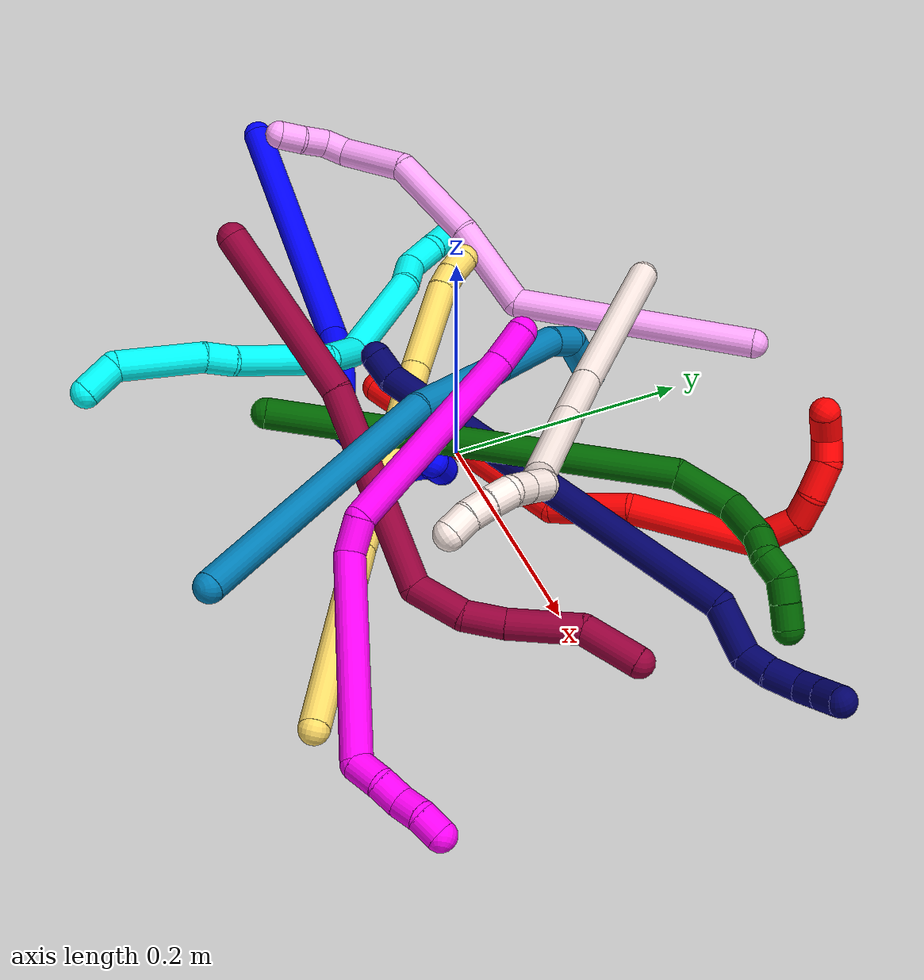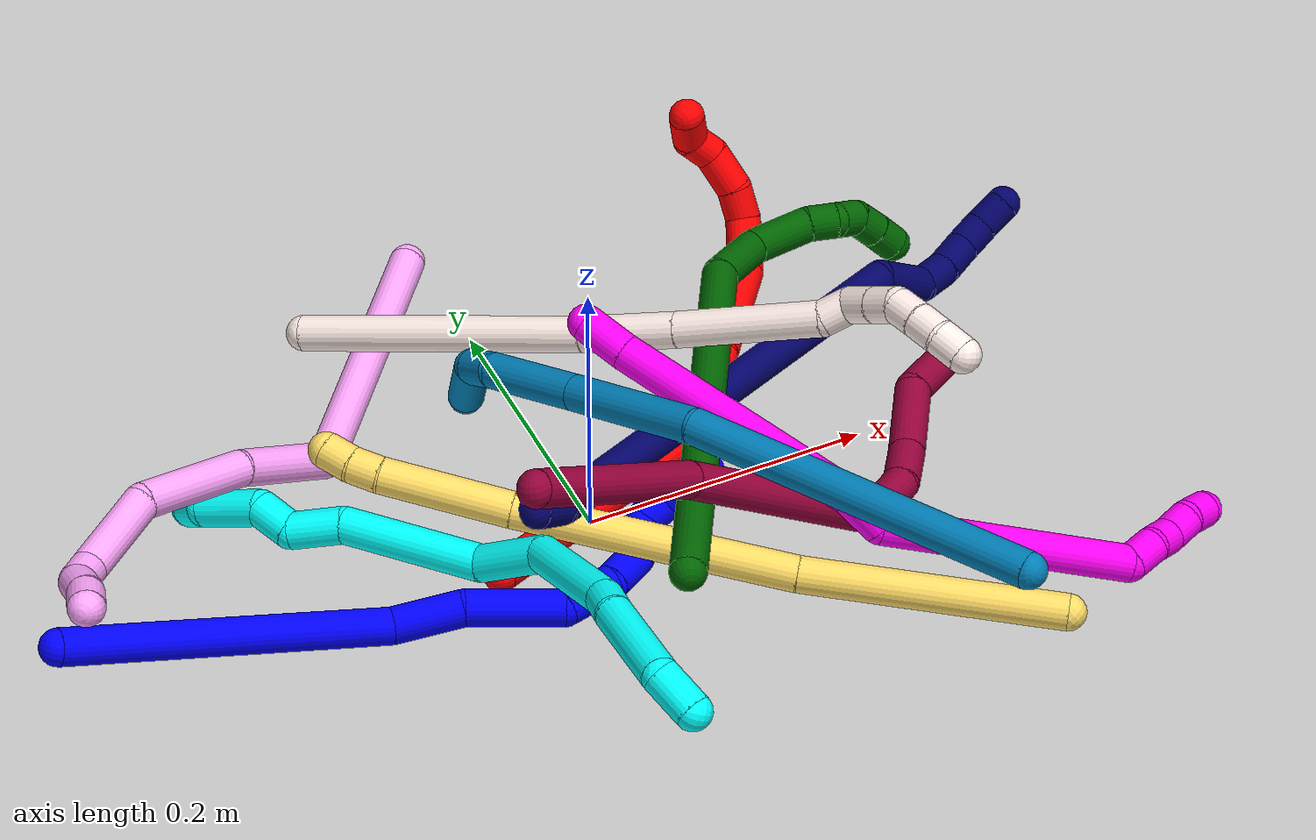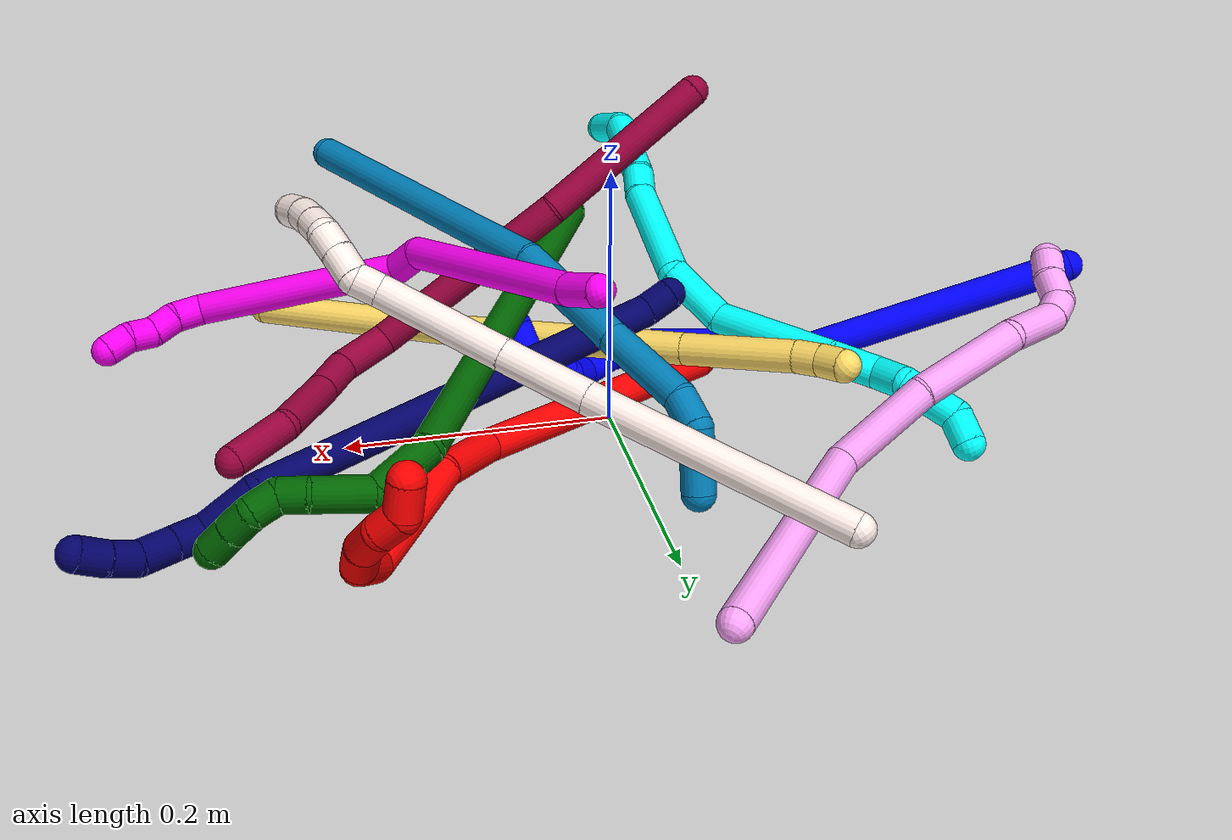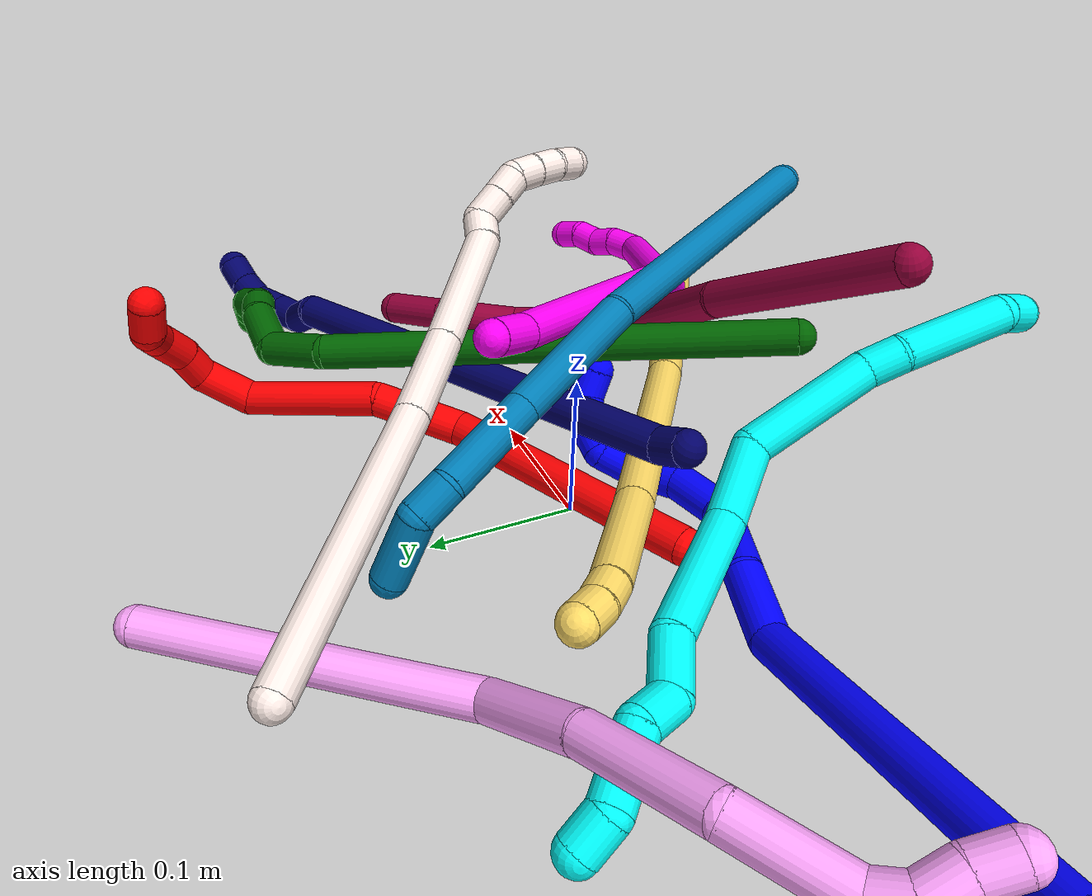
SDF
<sdf version="1.7">
 <world name="default">
  <plugin name="TubeGeneratorPlugin" filename="libtube_generator_plugin.so"/>
  <model name="photoneo_s_sensor">
   <static>1</static>
   <pose>0 0 2 1.57079 1.57079 3.14159</pose>
   <link name="link">
    <inertial><mass>0.1</mass></inertial>
    <sensor name="sensor" type="depth">
     <update_rate>30</update_rate>
     <camera>
      <horizontal_fov>1.22</horizontal_fov>
      <image><width>1920</width><height>1200</height><format>B8G8R8</format></image>
      <clip><near>0.1</near><far>4</far></clip>
      <depth_camera><output>points</output></depth_camera>
     </camera>
     <plugin name="camera_plugin" filename="libgazebo_ros_depth_camera.so">
      <baseline>0.2</baseline>
      <alwaysOn>1</alwaysOn>
      <updateRate>0.0</updateRate>
      <cameraName>camera_ir</cameraName>
      <imageTopicName>/camera/color/image_raw</imageTopicName>
      <cameraInfoTopicName>/camera/color/camera_info</cameraInfoTopicName>
      <depthImageTopicName>/camera/depth/image_raw</depthImageTopicName>
      <depthImageCameraInfoTopicName>/camera/depth/camera_info</depthImageCameraInfoTopicName>
      <pointCloudTopicName>/camera/depth/points</pointCloudTopicName>
      <frameName>fr_optical</frameName>
      <pointCloudCutoff>0.1</pointCloudCutoff>
      <pointCloudCutoffMax>2.0</pointCloudCutoffMax>
      <distortionK1>0</distortionK1>
      <distortionK2>0</distortionK2>
      <distortionK3>0</distortionK3>
      <distortionT1>0</distortionT1>
      <distortionT2>0</distortionT2>
      <CxPrime>0</CxPrime>
      <Cx>0</Cx>
      <Cy>0</Cy>
      <focalLength>0</focalLength>
      <hackBaseline>0</hackBaseline>
     </plugin>
    </sensor>
   </link>
  </model>
  <gravity>0 0 -9.8</gravity>
  <magnetic_field>6e-06 2.3e-05 -4.2e-05</magnetic_field>
  <atmosphere type="adiabatic"/>
  <physics name="default_physics" default="0" type="ode">
   <max_step_size>0.003</max_step_size>
   <real_time_factor>1</real_time_factor>
   <real_time_update_rate>1000</real_time_update_rate>
   <max_contacts>10000</max_contacts>
   <ode>
    <solver>
     <type>quick</type>
     <iters>100</iters>
     <sor>1.3</sor>
     <use_dynamic_moi_rescaling>0</use_dynamic_moi_rescaling>
    </solver>
    <constraints>
     <contact_max_correcting_vel>0</contact_max_correcting_vel>
     <contact_surface_layer>0.001</contact_surface_layer>
     <cfm>0</cfm>
     <erp>0.2</erp>
    </constraints>
   </ode>
  </physics>
  <scene><ambient>0.4 0.4 0.4 1</ambient><background>0.7 0.7 0.7 1</background><shadows>0</shadows></scene>
  <audio><device>default</device></audio>
  <spherical_coordinates>
   <surface_model>EARTH_WGS84</surface_model>
   <latitude_deg>0</latitude_deg>
   <longitude_deg>0</longitude_deg>
   <elevation>0</elevation>
   <heading_deg>0</heading_deg>
  </spherical_coordinates>
  <model name="bin">
   <static>1</static>
   <link name="bottom">
    <collision name="collision-bottom">
     <pose>0 0 -0.01 0 -0 0</pose>
     <geometry><box><size>0.8 0.6 0.02</size></box></geometry>
     <surface>
      <friction><ode><mu>100</mu><mu2>100</mu2></ode></friction>
      <contact><collide_bitmask>65535</collide_bitmask></contact>
     </surface>
    </collision>
   </link>
   <link name="west_wall">
    <collision name="collision-west_wall">
     <pose>-0.41 0 0.1 0 -0 0</pose>
     <geometry><box><size>0.02 0.6 0.2</size></box></geometry>
     <surface>
      <friction><ode><mu>100</mu><mu2>100</mu2></ode></friction>
      <contact><collide_bitmask>65535</collide_bitmask></contact>
     </surface>
    </collision>
   </link>
   <link name="east_wall">
    <collision name="collision-east_wall">
     <pose>0.41 0 0.1 0 -0 0</pose>
     <geometry><box><size>0.02 0.6 0.2</size></box></geometry>
     <surface>
      <friction><ode><mu>100</mu><mu2>100</mu2></ode></friction>
      <contact><collide_bitmask>65535</collide_bitmask></contact>
     </surface>
    </collision>
   </link>
   <link name="south_wall">
    <collision name="collision-south_wall">
     <pose>0 -0.31 0.1 0 -0 0</pose>
     <geometry><box><size>0.8 0.02 0.2</size></box></geometry>
     <surface>
      <friction><ode><mu>100</mu><mu2>100</mu2></ode></friction>
      <contact><collide_bitmask>65535</collide_bitmask></contact>
     </surface>
    </collision>
   </link>
   <link name="north_wall">
    <collision name="collision-north_wall">
     <pose>0 0.31 0.1 0 -0 0</pose>
     <geometry><box><size>0.8 0.02 0.2</size></box></geometry>
     <surface>
      <friction><ode><mu>100</mu><mu2>100</mu2></ode></friction>
      <contact><collide_bitmask>65535</collide_bitmask></contact>
     </surface>
    </collision>
   </link>
  </model>
  <model name="1">
   <static>0</static>
   <link name="1">
    <collision name="collision-cylinder-e_1_1_4">
     <pose>0.049863 0.018361 -0.10019 -2.96034 0.455232 -2.39384</pose>
     <geometry><cylinder><radius>0.0125</radius><length>0.226817</length></cylinder></geometry>
     <surface>
      <friction><ode><mu>1.16</mu><mu2>1.16</mu2><slip1>0</slip1><slip2>0</slip2></ode></friction>
      <contact><ode><kp>1e+06</kp><kd>1</kd><max_vel>0</max_vel><min_depth>0.001</min_depth></ode></contact>
     </surface>
    </collision>
    <visual name="visual-cylinder-e_1_1_4">
     <pose>0.049863 0.018361 -0.10019 -2.96034 0.455232 -2.39384</pose>
     <geometry><cylinder><radius>0.0125</radius><length>0.226817</length></cylinder></geometry>
     <material><ambient>0 0 1 1</ambient></material>
    </visual>
    <collision name="collision-cylinder-e_2_4_5">
     <pose>0.108578 0.029643 -0.221955 2.82448 0.371749 1.73224</pose>
     <geometry><cylinder><radius>0.0125</radius><length>0.048741</length></cylinder></geometry>
     <surface>
      <friction><ode><mu>1.16</mu><mu2>1.16</mu2><slip1>0</slip1><slip2>0</slip2></ode></friction>
      <contact><ode><kp>1e+06</kp><kd>1</kd><max_vel>0</max_vel><min_depth>0.001</min_depth></ode></contact>
     </surface>
    </collision>
    <visual name="visual-cylinder-e_2_4_5">
     <pose>0.108578 0.029643 -0.221955 2.82448 0.371749 1.73224</pose>
     <geometry><cylinder><radius>0.0125</radius><length>0.048741</length></cylinder></geometry>
     <material><ambient>0 0 1 1</ambient></material>
    </visual>
    <collision name="collision-cylinder-e_3_5_6">
     <pose>0.124726 0.019657 -0.275487 3.05092 0.22356 2.3734</pose>
     <geometry><cylinder><radius>0.0125</radius><length>0.065819</length></cylinder></geometry>
     <surface>
      <friction><ode><mu>1.16</mu><mu2>1.16</mu2><slip1>0</slip1><slip2>0</slip2></ode></friction>
      <contact><ode><kp>1e+06</kp><kd>1</kd><max_vel>0</max_vel><min_depth>0.001</min_depth></ode></contact>
     </surface>
    </collision>
    <visual name="visual-cylinder-e_3_5_6">
     <pose>0.124726 0.019657 -0.275487 3.05092 0.22356 2.3734</pose>
     <geometry><cylinder><radius>0.0125</radius><length>0.065819</length></cylinder></geometry>
     <material><ambient>0 0 1 1</ambient></material>
    </visual>
    <collision name="collision-cylinder-e_4_6_7">
     <pose>0.146202 0.016518 -0.320478 3.1237 0.827481 3.10085</pose>
     <geometry><cylinder><radius>0.0125</radius><length>0.038519</length></cylinder></geometry>
     <surface>
      <friction><ode><mu>1.16</mu><mu2>1.16</mu2><slip1>0</slip1><slip2>0</slip2></ode></friction>
      <contact><ode><kp>1e+06</kp><kd>1</kd><max_vel>0</max_vel><min_depth>0.001</min_depth></ode></contact>
     </surface>
    </collision>
    <visual name="visual-cylinder-e_4_6_7">
     <pose>0.146202 0.016518 -0.320478 3.1237 0.827481 3.10085</pose>
     <geometry><cylinder><radius>0.0125</radius><length>0.038519</length></cylinder></geometry>
     <material><ambient>0 0 1 1</ambient></material>
    </visual>
    <collision name="collision-cylinder-e_5_7_8">
     <pose>0.174173 0.018884 -0.340005 -2.76087 1.10132 -2.53341</pose>
     <geometry><cylinder><radius>0.0125</radius><length>0.03093</length></cylinder></geometry>
     <surface>
      <friction><ode><mu>1.16</mu><mu2>1.16</mu2><slip1>0</slip1><slip2>0</slip2></ode></friction>
      <contact><ode><kp>1e+06</kp><kd>1</kd><max_vel>0</max_vel><min_depth>0.001</min_depth></ode></contact>
     </surface>
    </collision>
    <visual name="visual-cylinder-e_5_7_8">
     <pose>0.174173 0.018884 -0.340005 -2.76087 1.10132 -2.53341</pose>
     <geometry><cylinder><radius>0.0125</radius><length>0.03093</length></cylinder></geometry>
     <material><ambient>0 0 1 1</ambient></material>
    </visual>
    <collision name="collision-cylinder-e_6_8_9">
     <pose>0.201603 0.017918 -0.346463 1.56031 1.31498 1.30485</pose>
     <geometry><cylinder><radius>0.0125</radius><length>0.028193</length></cylinder></geometry>
     <surface>
      <friction><ode><mu>1.16</mu><mu2>1.16</mu2><slip1>0</slip1><slip2>0</slip2></ode></friction>
      <contact><ode><kp>1e+06</kp><kd>1</kd><max_vel>0</max_vel><min_depth>0.001</min_depth></ode></contact>
     </surface>
    </collision>
    <visual name="visual-cylinder-e_6_8_9">
     <pose>0.201603 0.017918 -0.346463 1.56031 1.31498 1.30485</pose>
     <geometry><cylinder><radius>0.0125</radius><length>0.028193</length></cylinder></geometry>
     <material><ambient>0 0 1 1</ambient></material>
    </visual>
    <collision name="collision-cylinder-e_7_9_10">
     <pose>0.221453 0.009443 -0.352693 2.47731 0.662696 1.56822</pose>
     <geometry><cylinder><radius>0.0125</radius><length>0.020195</length></cylinder></geometry>
     <surface>
      <friction><ode><mu>1.16</mu><mu2>1.16</mu2><slip1>0</slip1><slip2>0</slip2></ode></friction>
      <contact><ode><kp>1e+06</kp><kd>1</kd><max_vel>0</max_vel><min_depth>0.001</min_depth></ode></contact>
     </surface>
    </collision>
    <visual name="visual-cylinder-e_7_9_10">
     <pose>0.221453 0.009443 -0.352693 2.47731 0.662696 1.56822</pose>
     <geometry><cylinder><radius>0.0125</radius><length>0.020195</length></cylinder></geometry>
     <material><ambient>0 0 1 1</ambient></material>
    </visual>
    <collision name="collision-cylinder-e_8_10_11">
     <pose>0.230986 -0.003279 -0.364659 2.2008 0.3307 0.634228</pose>
     <geometry><cylinder><radius>0.0125</radius><length>0.020452</length></cylinder></geometry>
     <surface>
      <friction><ode><mu>1.16</mu><mu2>1.16</mu2><slip1>0</slip1><slip2>0</slip2></ode></friction>
      <contact><ode><kp>1e+06</kp><kd>1</kd><max_vel>0</max_vel><min_depth>0.001</min_depth></ode></contact>
     </surface>
    </collision>
    <visual name="visual-cylinder-e_8_10_11">
     <pose>0.230986 -0.003279 -0.364659 2.2008 0.3307 0.634228</pose>
     <geometry><cylinder><radius>0.0125</radius><length>0.020452</length></cylinder></geometry>
     <material><ambient>0 0 1 1</ambient></material>
    </visual>
    <collision name="collision-cylinder-e_9_11_2">
     <pose>0.233236 -0.020666 -0.373612 1.89863 -0.105444 -0.147108</pose>
     <geometry><cylinder><radius>0.0125</radius><length>0.020333</length></cylinder></geometry>
     <surface>
      <friction><ode><mu>1.16</mu><mu2>1.16</mu2><slip1>0</slip1><slip2>0</slip2></ode></friction>
      <contact><ode><kp>1e+06</kp><kd>1</kd><max_vel>0</max_vel><min_depth>0.001</min_depth></ode></contact>
     </surface>
    </collision>
    <visual name="visual-cylinder-e_9_11_2">
     <pose>0.233236 -0.020666 -0.373612 1.89863 -0.105444 -0.147108</pose>
     <geometry><cylinder><radius>0.0125</radius><length>0.020333</length></cylinder></geometry>
     <material><ambient>0 0 1 1</ambient></material>
    </visual>
    <collision name="collision-sphere-2">
     <pose>0.232166 -0.030238 -0.376867 0 -0 0</pose>
     <geometry><sphere><radius>0.0125</radius></sphere></geometry>
     <surface>
      <friction><ode><mu>1.16</mu><mu2>1.16</mu2><slip1>0</slip1><slip2>0</slip2></ode></friction>
      <contact><ode><kp>1e+06</kp><kd>1</kd><max_vel>0</max_vel><min_depth>0.001</min_depth></ode></contact>
     </surface>
    </collision>
    <visual name="visual-sphere-2">
     <pose>0.232166 -0.030238 -0.376867 0 -0 0</pose>
     <geometry><sphere><radius>0.0125</radius></sphere></geometry>
     <material><ambient>0 0 1 1</ambient></material>
    </visual>
    <collision name="collision-sphere-11">
     <pose>0.234306 -0.011094 -0.370357 0 -0 0</pose>
     <geometry><sphere><radius>0.0125</radius></sphere></geometry>
     <surface>
      <friction><ode><mu>1.16</mu><mu2>1.16</mu2><slip1>0</slip1><slip2>0</slip2></ode></friction>
      <contact><ode><kp>1e+06</kp><kd>1</kd><max_vel>0</max_vel><min_depth>0.001</min_depth></ode></contact>
     </surface>
    </collision>
    <visual name="visual-sphere-11">
     <pose>0.234306 -0.011094 -0.370357 0 -0 0</pose>
     <geometry><sphere><radius>0.0125</radius></sphere></geometry>
     <material><ambient>0 0 1 1</ambient></material>
    </visual>
    <collision name="collision-sphere-10">
     <pose>0.227665 0.004536 -0.35896 0 -0 0</pose>
     <geometry><sphere><radius>0.0125</radius></sphere></geometry>
     <surface>
      <friction><ode><mu>1.16</mu><mu2>1.16</mu2><slip1>0</slip1><slip2>0</slip2></ode></friction>
      <contact><ode><kp>1e+06</kp><kd>1</kd><max_vel>0</max_vel><min_depth>0.001</min_depth></ode></contact>
     </surface>
    </collision>
    <visual name="visual-sphere-10">
     <pose>0.227665 0.004536 -0.35896 0 -0 0</pose>
     <geometry><sphere><radius>0.0125</radius></sphere></geometry>
     <material><ambient>0 0 1 1</ambient></material>
    </visual>
    <collision name="collision-sphere-9">
     <pose>0.215241 0.014351 -0.346426 0 -0 0</pose>
     <geometry><sphere><radius>0.0125</radius></sphere></geometry>
     <surface>
      <friction><ode><mu>1.16</mu><mu2>1.16</mu2><slip1>0</slip1><slip2>0</slip2></ode></friction>
      <contact><ode><kp>1e+06</kp><kd>1</kd><max_vel>0</max_vel><min_depth>0.001</min_depth></ode></contact>
     </surface>
    </collision>
    <visual name="visual-sphere-9">
     <pose>0.215241 0.014351 -0.346426 0 -0 0</pose>
     <geometry><sphere><radius>0.0125</radius></sphere></geometry>
     <material><ambient>0 0 1 1</ambient></material>
    </visual>
    <collision name="collision-sphere-4">
     <pose>0.099725 0.036723 -0.200381 0 -0 0</pose>
     <geometry><sphere><radius>0.0125</radius></sphere></geometry>
     <surface>
      <friction><ode><mu>1.16</mu><mu2>1.16</mu2><slip1>0</slip1><slip2>0</slip2></ode></friction>
      <contact><ode><kp>1e+06</kp><kd>1</kd><max_vel>0</max_vel><min_depth>0.001</min_depth></ode></contact>
     </surface>
    </collision>
    <visual name="visual-sphere-4">
     <pose>0.099725 0.036723 -0.200381 0 -0 0</pose>
     <geometry><sphere><radius>0.0125</radius></sphere></geometry>
     <material><ambient>0 0 1 1</ambient></material>
    </visual>
    <collision name="collision-sphere-1">
     <geometry><sphere><radius>0.0125</radius></sphere></geometry>
     <surface>
      <friction><ode><mu>1.16</mu><mu2>1.16</mu2><slip1>0</slip1><slip2>0</slip2></ode></friction>
      <contact><ode><kp>1e+06</kp><kd>1</kd><max_vel>0</max_vel><min_depth>0.001</min_depth></ode></contact>
     </surface>
    </collision>
    <visual name="visual-sphere-1">
     <geometry><sphere><radius>0.0125</radius></sphere></geometry>
     <material><ambient>0 0 1 1</ambient></material>
    </visual>
    <collision name="collision-sphere-8">
     <pose>0.187965 0.021484 -0.3465 0 -0 0</pose>
     <geometry><sphere><radius>0.0125</radius></sphere></geometry>
     <surface>
      <friction><ode><mu>1.16</mu><mu2>1.16</mu2><slip1>0</slip1><slip2>0</slip2></ode></friction>
      <contact><ode><kp>1e+06</kp><kd>1</kd><max_vel>0</max_vel><min_depth>0.001</min_depth></ode></contact>
     </surface>
    </collision>
    <visual name="visual-sphere-8">
     <pose>0.187965 0.021484 -0.3465 0 -0 0</pose>
     <geometry><sphere><radius>0.0125</radius></sphere></geometry>
     <material><ambient>0 0 1 1</ambient></material>
    </visual>
    <collision name="collision-sphere-5">
     <pose>0.11743 0.022562 -0.243529 0 -0 0</pose>
     <geometry><sphere><radius>0.0125</radius></sphere></geometry>
     <surface>
      <friction><ode><mu>1.16</mu><mu2>1.16</mu2><slip1>0</slip1><slip2>0</slip2></ode></friction>
      <contact><ode><kp>1e+06</kp><kd>1</kd><max_vel>0</max_vel><min_depth>0.001</min_depth></ode></contact>
     </surface>
    </collision>
    <visual name="visual-sphere-5">
     <pose>0.11743 0.022562 -0.243529 0 -0 0</pose>
     <geometry><sphere><radius>0.0125</radius></sphere></geometry>
     <material><ambient>0 0 1 1</ambient></material>
    </visual>
    <collision name="collision-sphere-6">
     <pose>0.132022 0.016751 -0.307446 0 -0 0</pose>
     <geometry><sphere><radius>0.0125</radius></sphere></geometry>
     <surface>
      <friction><ode><mu>1.16</mu><mu2>1.16</mu2><slip1>0</slip1><slip2>0</slip2></ode></friction>
      <contact><ode><kp>1e+06</kp><kd>1</kd><max_vel>0</max_vel><min_depth>0.001</min_depth></ode></contact>
     </surface>
    </collision>
    <visual name="visual-sphere-6">
     <pose>0.132022 0.016751 -0.307446 0 -0 0</pose>
     <geometry><sphere><radius>0.0125</radius></sphere></geometry>
     <material><ambient>0 0 1 1</ambient></material>
    </visual>
    <collision name="collision-sphere-7">
     <pose>0.160381 0.016285 -0.333509 0 -0 0</pose>
     <geometry><sphere><radius>0.0125</radius></sphere></geometry>
     <surface>
      <friction><ode><mu>1.16</mu><mu2>1.16</mu2><slip1>0</slip1><slip2>0</slip2></ode></friction>
      <contact><ode><kp>1e+06</kp><kd>1</kd><max_vel>0</max_vel><min_depth>0.001</min_depth></ode></contact>
     </surface>
    </collision>
    <visual name="visual-sphere-7">
     <pose>0.160381 0.016285 -0.333509 0 -0 0</pose>
     <geometry><sphere><radius>0.0125</radius></sphere></geometry>
     <material><ambient>0 0 1 1</ambient></material>
    </visual>
    <inertial>
     <pose>0.110905 0.016664 -0.212963 0 -0 0</pose>
     <mass>0.5</mass>
     <inertia>
      <ixx>-0.00122</ixx>
      <ixy>0</ixy>
      <ixz>0</ixz>
      <iyy>0.000224</iyy>
      <iyz>0</iyz>
      <izz>-0.000633</izz>
     </inertia>
    </inertial>
   </link>
   <pose>-0.380645 -0.029143 0.073387 -1.36033 -0.161684 0.966468</pose>
  </model>
  <model name="2">
   <static>0</static>
   <link name="2">
    <collision name="collision-cylinder-e_1_1_4">
     <pose>-0.001494 -0.000691 0.098515 0.00701 -0.015159 -5.3e-05</pose>
     <geometry><cylinder><radius>0.0125</radius><length>0.197058</length></cylinder></geometry>
     <surface>
      <friction><ode><mu>1.16</mu><mu2>1.16</mu2><slip1>0</slip1><slip2>0</slip2></ode></friction>
      <contact><ode><kp>1e+06</kp><kd>1</kd><max_vel>0</max_vel><min_depth>0.001</min_depth></ode></contact>
     </surface>
    </collision>
    <visual name="visual-cylinder-e_1_1_4">
     <pose>-0.001494 -0.000691 0.098515 0.00701 -0.015159 -5.3e-05</pose>
     <geometry><cylinder><radius>0.0125</radius><length>0.197058</length></cylinder></geometry>
     <material><ambient>1 0 0 1</ambient></material>
    </visual>
    <collision name="collision-cylinder-e_2_4_5">
     <pose>0.005417 0.013632 0.224574 -0.49906 0.261754 -0.067064</pose>
     <geometry><cylinder><radius>0.0125</radius><length>0.064951</length></cylinder></geometry>
     <surface>
      <friction><ode><mu>1.16</mu><mu2>1.16</mu2><slip1>0</slip1><slip2>0</slip2></ode></friction>
      <contact><ode><kp>1e+06</kp><kd>1</kd><max_vel>0</max_vel><min_depth>0.001</min_depth></ode></contact>
     </surface>
    </collision>
    <visual name="visual-cylinder-e_2_4_5">
     <pose>0.005417 0.013632 0.224574 -0.49906 0.261754 -0.067064</pose>
     <geometry><cylinder><radius>0.0125</radius><length>0.064951</length></cylinder></geometry>
     <material><ambient>1 0 0 1</ambient></material>
    </visual>
    <collision name="collision-cylinder-e_3_5_6">
     <pose>0.038214 0.03717 0.295959 -0.192039 0.499888 -0.049165</pose>
     <geometry><cylinder><radius>0.0125</radius><length>0.101781</length></cylinder></geometry>
     <surface>
      <friction><ode><mu>1.16</mu><mu2>1.16</mu2><slip1>0</slip1><slip2>0</slip2></ode></friction>
      <contact><ode><kp>1e+06</kp><kd>1</kd><max_vel>0</max_vel><min_depth>0.001</min_depth></ode></contact>
     </surface>
    </collision>
    <visual name="visual-cylinder-e_3_5_6">
     <pose>0.038214 0.03717 0.295959 -0.192039 0.499888 -0.049165</pose>
     <geometry><cylinder><radius>0.0125</radius><length>0.101781</length></cylinder></geometry>
     <material><ambient>1 0 0 1</ambient></material>
    </visual>
    <collision name="collision-cylinder-e_4_6_7">
     <pose>0.066772 0.061192 0.351456 -0.926006 0.211577 -0.105915</pose>
     <geometry><cylinder><radius>0.0125</radius><length>0.039667</length></cylinder></geometry>
     <surface>
      <friction><ode><mu>1.16</mu><mu2>1.16</mu2><slip1>0</slip1><slip2>0</slip2></ode></friction>
      <contact><ode><kp>1e+06</kp><kd>1</kd><max_vel>0</max_vel><min_depth>0.001</min_depth></ode></contact>
     </surface>
    </collision>
    <visual name="visual-cylinder-e_4_6_7">
     <pose>0.066772 0.061192 0.351456 -0.926006 0.211577 -0.105915</pose>
     <geometry><cylinder><radius>0.0125</radius><length>0.039667</length></cylinder></geometry>
     <material><ambient>1 0 0 1</ambient></material>
    </visual>
    <collision name="collision-cylinder-e_5_7_8">
     <pose>0.070237 0.088502 0.363978 -1.4975 -0.058987 0.054817</pose>
     <geometry><cylinder><radius>0.0125</radius><length>0.023728</length></cylinder></geometry>
     <surface>
      <friction><ode><mu>1.16</mu><mu2>1.16</mu2><slip1>0</slip1><slip2>0</slip2></ode></friction>
      <contact><ode><kp>1e+06</kp><kd>1</kd><max_vel>0</max_vel><min_depth>0.001</min_depth></ode></contact>
     </surface>
    </collision>
    <visual name="visual-cylinder-e_5_7_8">
     <pose>0.070237 0.088502 0.363978 -1.4975 -0.058987 0.054817</pose>
     <geometry><cylinder><radius>0.0125</radius><length>0.023728</length></cylinder></geometry>
     <material><ambient>1 0 0 1</ambient></material>
    </visual>
    <collision name="collision-cylinder-e_6_8_9">
     <pose>0.072145 0.114453 0.363314 -1.67871 0.181268 -0.201833</pose>
     <geometry><cylinder><radius>0.0125</radius><length>0.028918</length></cylinder></geometry>
     <surface>
      <friction><ode><mu>1.16</mu><mu2>1.16</mu2><slip1>0</slip1><slip2>0</slip2></ode></friction>
      <contact><ode><kp>1e+06</kp><kd>1</kd><max_vel>0</max_vel><min_depth>0.001</min_depth></ode></contact>
     </surface>
    </collision>
    <visual name="visual-cylinder-e_6_8_9">
     <pose>0.072145 0.114453 0.363314 -1.67871 0.181268 -0.201833</pose>
     <geometry><cylinder><radius>0.0125</radius><length>0.028918</length></cylinder></geometry>
     <material><ambient>1 0 0 1</ambient></material>
    </visual>
    <collision name="collision-cylinder-e_7_9_10">
     <pose>0.076073 0.137009 0.356495 -2.13171 0.132247 -0.238471</pose>
     <geometry><cylinder><radius>0.0125</radius><length>0.020053</length></cylinder></geometry>
     <surface>
      <friction><ode><mu>1.16</mu><mu2>1.16</mu2><slip1>0</slip1><slip2>0</slip2></ode></friction>
      <contact><ode><kp>1e+06</kp><kd>1</kd><max_vel>0</max_vel><min_depth>0.001</min_depth></ode></contact>
     </surface>
    </collision>
    <visual name="visual-cylinder-e_7_9_10">
     <pose>0.076073 0.137009 0.356495 -2.13171 0.132247 -0.238471</pose>
     <geometry><cylinder><radius>0.0125</radius><length>0.020053</length></cylinder></geometry>
     <material><ambient>1 0 0 1</ambient></material>
    </visual>
    <collision name="collision-cylinder-e_8_10_2">
     <pose>0.071281 0.155308 0.348553 -1.83323 -0.538588 0.690978</pose>
     <geometry><cylinder><radius>0.0125</radius><length>0.023843</length></cylinder></geometry>
     <surface>
      <friction><ode><mu>1.16</mu><mu2>1.16</mu2><slip1>0</slip1><slip2>0</slip2></ode></friction>
      <contact><ode><kp>1e+06</kp><kd>1</kd><max_vel>0</max_vel><min_depth>0.001</min_depth></ode></contact>
     </surface>
    </collision>
    <visual name="visual-cylinder-e_8_10_2">
     <pose>0.071281 0.155308 0.348553 -1.83323 -0.538588 0.690978</pose>
     <geometry><cylinder><radius>0.0125</radius><length>0.023843</length></cylinder></geometry>
     <material><ambient>1 0 0 1</ambient></material>
    </visual>
    <collision name="collision-sphere-2">
     <pose>0.065166 0.165192 0.345898 0 -0 0</pose>
     <geometry><sphere><radius>0.0125</radius></sphere></geometry>
     <surface>
      <friction><ode><mu>1.16</mu><mu2>1.16</mu2><slip1>0</slip1><slip2>0</slip2></ode></friction>
      <contact><ode><kp>1e+06</kp><kd>1</kd><max_vel>0</max_vel><min_depth>0.001</min_depth></ode></contact>
     </surface>
    </collision>
    <visual name="visual-sphere-2">
     <pose>0.065166 0.165192 0.345898 0 -0 0</pose>
     <geometry><sphere><radius>0.0125</radius></sphere></geometry>
     <material><ambient>1 0 0 1</ambient></material>
    </visual>
    <collision name="collision-sphere-10">
     <pose>0.077396 0.145425 0.351208 0 -0 0</pose>
     <geometry><sphere><radius>0.0125</radius></sphere></geometry>
     <surface>
      <friction><ode><mu>1.16</mu><mu2>1.16</mu2><slip1>0</slip1><slip2>0</slip2></ode></friction>
      <contact><ode><kp>1e+06</kp><kd>1</kd><max_vel>0</max_vel><min_depth>0.001</min_depth></ode></contact>
     </surface>
    </collision>
    <visual name="visual-sphere-10">
     <pose>0.077396 0.145425 0.351208 0 -0 0</pose>
     <geometry><sphere><radius>0.0125</radius></sphere></geometry>
     <material><ambient>1 0 0 1</ambient></material>
    </visual>
    <collision name="collision-sphere-9">
     <pose>0.074751 0.128593 0.361782 0 -0 0</pose>
     <geometry><sphere><radius>0.0125</radius></sphere></geometry>
     <surface>
      <friction><ode><mu>1.16</mu><mu2>1.16</mu2><slip1>0</slip1><slip2>0</slip2></ode></friction>
      <contact><ode><kp>1e+06</kp><kd>1</kd><max_vel>0</max_vel><min_depth>0.001</min_depth></ode></contact>
     </surface>
    </collision>
    <visual name="visual-sphere-9">
     <pose>0.074751 0.128593 0.361782 0 -0 0</pose>
     <geometry><sphere><radius>0.0125</radius></sphere></geometry>
     <material><ambient>1 0 0 1</ambient></material>
    </visual>
    <collision name="collision-sphere-4">
     <pose>-0.002987 -0.001381 0.197031 0 -0 0</pose>
     <geometry><sphere><radius>0.0125</radius></sphere></geometry>
     <surface>
      <friction><ode><mu>1.16</mu><mu2>1.16</mu2><slip1>0</slip1><slip2>0</slip2></ode></friction>
      <contact><ode><kp>1e+06</kp><kd>1</kd><max_vel>0</max_vel><min_depth>0.001</min_depth></ode></contact>
     </surface>
    </collision>
    <visual name="visual-sphere-4">
     <pose>-0.002987 -0.001381 0.197031 0 -0 0</pose>
     <geometry><sphere><radius>0.0125</radius></sphere></geometry>
     <material><ambient>1 0 0 1</ambient></material>
    </visual>
    <collision name="collision-sphere-1">
     <geometry><sphere><radius>0.0125</radius></sphere></geometry>
     <surface>
      <friction><ode><mu>1.16</mu><mu2>1.16</mu2><slip1>0</slip1><slip2>0</slip2></ode></friction>
      <contact><ode><kp>1e+06</kp><kd>1</kd><max_vel>0</max_vel><min_depth>0.001</min_depth></ode></contact>
     </surface>
    </collision>
    <visual name="visual-sphere-1">
     <geometry><sphere><radius>0.0125</radius></sphere></geometry>
     <material><ambient>1 0 0 1</ambient></material>
    </visual>
    <collision name="collision-sphere-8">
     <pose>0.069538 0.100314 0.364846 0 -0 0</pose>
     <geometry><sphere><radius>0.0125</radius></sphere></geometry>
     <surface>
      <friction><ode><mu>1.16</mu><mu2>1.16</mu2><slip1>0</slip1><slip2>0</slip2></ode></friction>
      <contact><ode><kp>1e+06</kp><kd>1</kd><max_vel>0</max_vel><min_depth>0.001</min_depth></ode></contact>
     </surface>
    </collision>
    <visual name="visual-sphere-8">
     <pose>0.069538 0.100314 0.364846 0 -0 0</pose>
     <geometry><sphere><radius>0.0125</radius></sphere></geometry>
     <material><ambient>1 0 0 1</ambient></material>
    </visual>
    <collision name="collision-sphere-5">
     <pose>0.01382 0.028645 0.252117 0 -0 0</pose>
     <geometry><sphere><radius>0.0125</radius></sphere></geometry>
     <surface>
      <friction><ode><mu>1.16</mu><mu2>1.16</mu2><slip1>0</slip1><slip2>0</slip2></ode></friction>
      <contact><ode><kp>1e+06</kp><kd>1</kd><max_vel>0</max_vel><min_depth>0.001</min_depth></ode></contact>
     </surface>
    </collision>
    <visual name="visual-sphere-5">
     <pose>0.01382 0.028645 0.252117 0 -0 0</pose>
     <geometry><sphere><radius>0.0125</radius></sphere></geometry>
     <material><ambient>1 0 0 1</ambient></material>
    </visual>
    <collision name="collision-sphere-6">
     <pose>0.062607 0.045694 0.339802 0 -0 0</pose>
     <geometry><sphere><radius>0.0125</radius></sphere></geometry>
     <surface>
      <friction><ode><mu>1.16</mu><mu2>1.16</mu2><slip1>0</slip1><slip2>0</slip2></ode></friction>
      <contact><ode><kp>1e+06</kp><kd>1</kd><max_vel>0</max_vel><min_depth>0.001</min_depth></ode></contact>
     </surface>
    </collision>
    <visual name="visual-sphere-6">
     <pose>0.062607 0.045694 0.339802 0 -0 0</pose>
     <geometry><sphere><radius>0.0125</radius></sphere></geometry>
     <material><ambient>1 0 0 1</ambient></material>
    </visual>
    <collision name="collision-sphere-7">
     <pose>0.070937 0.07669 0.363111 0 -0 0</pose>
     <geometry><sphere><radius>0.0125</radius></sphere></geometry>
     <surface>
      <friction><ode><mu>1.16</mu><mu2>1.16</mu2><slip1>0</slip1><slip2>0</slip2></ode></friction>
      <contact><ode><kp>1e+06</kp><kd>1</kd><max_vel>0</max_vel><min_depth>0.001</min_depth></ode></contact>
     </surface>
    </collision>
    <visual name="visual-sphere-7">
     <pose>0.070937 0.07669 0.363111 0 -0 0</pose>
     <geometry><sphere><radius>0.0125</radius></sphere></geometry>
     <material><ambient>1 0 0 1</ambient></material>
    </visual>
    <inertial>
     <pose>0.027147 0.03764 0.225333 0 -0 0</pose>
     <mass>0.5</mass>
     <inertia>
      <ixx>0.000764</ixx>
      <ixy>0</ixy>
      <ixz>0</ixz>
      <iyy>0.000769</iyy>
      <iyz>0</iyz>
      <izz>-5.1e-05</izz>
     </inertia>
    </inertial>
   </link>
   <pose>-0.080873 -0.037088 0.019604 1.61859 0.543929 2.01179</pose>
  </model>
  <model name="3">
   <static>0</static>
   <link name="3">
    <collision name="collision-cylinder-e_1_1_4">
     <pose>0.00138 0.011677 0.009816 -0.871752 0.090233 -0.042049</pose>
     <geometry><cylinder><radius>0.0125</radius><length>0.030634</length></cylinder></geometry>
     <surface>
      <friction><ode><mu>1.16</mu><mu2>1.16</mu2><slip1>0</slip1><slip2>0</slip2></ode></friction>
      <contact><ode><kp>1e+06</kp><kd>1</kd><max_vel>0</max_vel><min_depth>0.001</min_depth></ode></contact>
     </surface>
    </collision>
    <visual name="visual-cylinder-e_1_1_4">
     <pose>0.00138 0.011677 0.009816 -0.871752 0.090233 -0.042049</pose>
     <geometry><cylinder><radius>0.0125</radius><length>0.030634</length></cylinder></geometry>
     <material><ambient>0.003922 1 0.996078 1</ambient></material>
    </visual>
    <collision name="collision-cylinder-e_2_4_5">
     <pose>-0.007136 0.058299 0.025647 -1.40036 -0.272158 0.229728</pose>
     <geometry><cylinder><radius>0.0125</radius><length>0.073629</length></cylinder></geometry>
     <surface>
      <friction><ode><mu>1.16</mu><mu2>1.16</mu2><slip1>0</slip1><slip2>0</slip2></ode></friction>
      <contact><ode><kp>1e+06</kp><kd>1</kd><max_vel>0</max_vel><min_depth>0.001</min_depth></ode></contact>
     </surface>
    </collision>
    <visual name="visual-cylinder-e_2_4_5">
     <pose>-0.007136 0.058299 0.025647 -1.40036 -0.272158 0.229728</pose>
     <geometry><cylinder><radius>0.0125</radius><length>0.073629</length></cylinder></geometry>
     <material><ambient>0.003922 1 0.996078 1</ambient></material>
    </visual>
    <collision name="collision-cylinder-e_3_5_6">
     <pose>-0.021584 0.104878 0.031255 -1.60569 -0.37279 0.38571</pose>
     <geometry><cylinder><radius>0.0125</radius><length>0.024997</length></cylinder></geometry>
     <surface>
      <friction><ode><mu>1.16</mu><mu2>1.16</mu2><slip1>0</slip1><slip2>0</slip2></ode></friction>
      <contact><ode><kp>1e+06</kp><kd>1</kd><max_vel>0</max_vel><min_depth>0.001</min_depth></ode></contact>
     </surface>
    </collision>
    <visual name="visual-cylinder-e_3_5_6">
     <pose>-0.021584 0.104878 0.031255 -1.60569 -0.37279 0.38571</pose>
     <geometry><cylinder><radius>0.0125</radius><length>0.024997</length></cylinder></geometry>
     <material><ambient>0.003922 1 0.996078 1</ambient></material>
    </visual>
    <collision name="collision-cylinder-e_4_6_7">
     <pose>-0.04642 0.154828 0.038142 -1.38273 -0.479533 0.399272</pose>
     <geometry><cylinder><radius>0.0125</radius><length>0.087928</length></cylinder></geometry>
     <surface>
      <friction><ode><mu>1.16</mu><mu2>1.16</mu2><slip1>0</slip1><slip2>0</slip2></ode></friction>
      <contact><ode><kp>1e+06</kp><kd>1</kd><max_vel>0</max_vel><min_depth>0.001</min_depth></ode></contact>
     </surface>
    </collision>
    <visual name="visual-cylinder-e_4_6_7">
     <pose>-0.04642 0.154828 0.038142 -1.38273 -0.479533 0.399272</pose>
     <geometry><cylinder><radius>0.0125</radius><length>0.087928</length></cylinder></geometry>
     <material><ambient>0.003922 1 0.996078 1</ambient></material>
    </visual>
    <collision name="collision-cylinder-e_5_7_8">
     <pose>-0.086307 0.205142 0.057216 -0.794406 -0.861825 0.381032</pose>
     <geometry><cylinder><radius>0.0125</radius><length>0.051654</length></cylinder></geometry>
     <surface>
      <friction><ode><mu>1.16</mu><mu2>1.16</mu2><slip1>0</slip1><slip2>0</slip2></ode></friction>
      <contact><ode><kp>1e+06</kp><kd>1</kd><max_vel>0</max_vel><min_depth>0.001</min_depth></ode></contact>
     </surface>
    </collision>
    <visual name="visual-cylinder-e_5_7_8">
     <pose>-0.086307 0.205142 0.057216 -0.794406 -0.861825 0.381032</pose>
     <geometry><cylinder><radius>0.0125</radius><length>0.051654</length></cylinder></geometry>
     <material><ambient>0.003922 1 0.996078 1</ambient></material>
    </visual>
    <collision name="collision-cylinder-e_6_8_9">
     <pose>-0.124092 0.24296 0.10725 -0.593778 -0.375295 0.116051</pose>
     <geometry><cylinder><radius>0.0125</radius><length>0.099206</length></cylinder></geometry>
     <surface>
      <friction><ode><mu>1.16</mu><mu2>1.16</mu2><slip1>0</slip1><slip2>0</slip2></ode></friction>
      <contact><ode><kp>1e+06</kp><kd>1</kd><max_vel>0</max_vel><min_depth>0.001</min_depth></ode></contact>
     </surface>
    </collision>
    <visual name="visual-cylinder-e_6_8_9">
     <pose>-0.124092 0.24296 0.10725 -0.593778 -0.375295 0.116051</pose>
     <geometry><cylinder><radius>0.0125</radius><length>0.099206</length></cylinder></geometry>
     <material><ambient>0.003922 1 0.996078 1</ambient></material>
    </visual>
    <collision name="collision-cylinder-e_7_9_10">
     <pose>-0.152969 0.272827 0.159847 -0.27485 -0.622349 0.0889</pose>
     <geometry><cylinder><radius>0.0125</radius><length>0.036692</length></cylinder></geometry>
     <surface>
      <friction><ode><mu>1.16</mu><mu2>1.16</mu2><slip1>0</slip1><slip2>0</slip2></ode></friction>
      <contact><ode><kp>1e+06</kp><kd>1</kd><max_vel>0</max_vel><min_depth>0.001</min_depth></ode></contact>
     </surface>
    </collision>
    <visual name="visual-cylinder-e_7_9_10">
     <pose>-0.152969 0.272827 0.159847 -0.27485 -0.622349 0.0889</pose>
     <geometry><cylinder><radius>0.0125</radius><length>0.036692</length></cylinder></geometry>
     <material><ambient>0.003922 1 0.996078 1</ambient></material>
    </visual>
    <collision name="collision-cylinder-e_8_10_11">
     <pose>-0.165557 0.287205 0.183178 -0.855107 -0.13744 0.062705</pose>
     <geometry><cylinder><radius>0.0125</radius><length>0.027644</length></cylinder></geometry>
     <surface>
      <friction><ode><mu>1.16</mu><mu2>1.16</mu2><slip1>0</slip1><slip2>0</slip2></ode></friction>
      <contact><ode><kp>1e+06</kp><kd>1</kd><max_vel>0</max_vel><min_depth>0.001</min_depth></ode></contact>
     </surface>
    </collision>
    <visual name="visual-cylinder-e_8_10_11">
     <pose>-0.165557 0.287205 0.183178 -0.855107 -0.13744 0.062705</pose>
     <geometry><cylinder><radius>0.0125</radius><length>0.027644</length></cylinder></geometry>
     <material><ambient>0.003922 1 0.996078 1</ambient></material>
    </visual>
    <collision name="collision-cylinder-e_9_11_12">
     <pose>-0.181473 0.307749 0.206148 -0.630641 -0.680632 0.229994</pose>
     <geometry><cylinder><radius>0.0125</radius><length>0.044566</length></cylinder></geometry>
     <surface>
      <friction><ode><mu>1.16</mu><mu2>1.16</mu2><slip1>0</slip1><slip2>0</slip2></ode></friction>
      <contact><ode><kp>1e+06</kp><kd>1</kd><max_vel>0</max_vel><min_depth>0.001</min_depth></ode></contact>
     </surface>
    </collision>
    <visual name="visual-cylinder-e_9_11_12">
     <pose>-0.181473 0.307749 0.206148 -0.630641 -0.680632 0.229994</pose>
     <geometry><cylinder><radius>0.0125</radius><length>0.044566</length></cylinder></geometry>
     <material><ambient>0.003922 1 0.996078 1</ambient></material>
    </visual>
    <collision name="collision-cylinder-e_10_12_2">
     <pose>-0.203686 0.325961 0.221452 -1.40761 -0.790422 0.680629</pose>
     <geometry><cylinder><radius>0.0125</radius><length>0.02305</length></cylinder></geometry>
     <surface>
      <friction><ode><mu>1.16</mu><mu2>1.16</mu2><slip1>0</slip1><slip2>0</slip2></ode></friction>
      <contact><ode><kp>1e+06</kp><kd>1</kd><max_vel>0</max_vel><min_depth>0.001</min_depth></ode></contact>
     </surface>
    </collision>
    <visual name="visual-cylinder-e_10_12_2">
     <pose>-0.203686 0.325961 0.221452 -1.40761 -0.790422 0.680629</pose>
     <geometry><cylinder><radius>0.0125</radius><length>0.02305</length></cylinder></geometry>
     <material><ambient>0.003922 1 0.996078 1</ambient></material>
    </visual>
    <collision name="collision-sphere-2">
     <pose>-0.211876 0.333962 0.22277 0 -0 0</pose>
     <geometry><sphere><radius>0.0125</radius></sphere></geometry>
     <surface>
      <friction><ode><mu>1.16</mu><mu2>1.16</mu2><slip1>0</slip1><slip2>0</slip2></ode></friction>
      <contact><ode><kp>1e+06</kp><kd>1</kd><max_vel>0</max_vel><min_depth>0.001</min_depth></ode></contact>
     </surface>
    </collision>
    <visual name="visual-sphere-2">
     <pose>-0.211876 0.333962 0.22277 0 -0 0</pose>
     <geometry><sphere><radius>0.0125</radius></sphere></geometry>
     <material><ambient>0.003922 1 0.996078 1</ambient></material>
    </visual>
    <collision name="collision-sphere-12">
     <pose>-0.195495 0.31796 0.220135 0 -0 0</pose>
     <geometry><sphere><radius>0.0125</radius></sphere></geometry>
     <surface>
      <friction><ode><mu>1.16</mu><mu2>1.16</mu2><slip1>0</slip1><slip2>0</slip2></ode></friction>
      <contact><ode><kp>1e+06</kp><kd>1</kd><max_vel>0</max_vel><min_depth>0.001</min_depth></ode></contact>
     </surface>
    </collision>
    <visual name="visual-sphere-12">
     <pose>-0.195495 0.31796 0.220135 0 -0 0</pose>
     <geometry><sphere><radius>0.0125</radius></sphere></geometry>
     <material><ambient>0.003922 1 0.996078 1</ambient></material>
    </visual>
    <collision name="collision-sphere-11">
     <pose>-0.167451 0.297537 0.192162 0 -0 0</pose>
     <geometry><sphere><radius>0.0125</radius></sphere></geometry>
     <surface>
      <friction><ode><mu>1.16</mu><mu2>1.16</mu2><slip1>0</slip1><slip2>0</slip2></ode></friction>
      <contact><ode><kp>1e+06</kp><kd>1</kd><max_vel>0</max_vel><min_depth>0.001</min_depth></ode></contact>
     </surface>
    </collision>
    <visual name="visual-sphere-11">
     <pose>-0.167451 0.297537 0.192162 0 -0 0</pose>
     <geometry><sphere><radius>0.0125</radius></sphere></geometry>
     <material><ambient>0.003922 1 0.996078 1</ambient></material>
    </visual>
    <collision name="collision-sphere-10">
     <pose>-0.163663 0.276872 0.174194 0 -0 0</pose>
     <geometry><sphere><radius>0.0125</radius></sphere></geometry>
     <surface>
      <friction><ode><mu>1.16</mu><mu2>1.16</mu2><slip1>0</slip1><slip2>0</slip2></ode></friction>
      <contact><ode><kp>1e+06</kp><kd>1</kd><max_vel>0</max_vel><min_depth>0.001</min_depth></ode></contact>
     </surface>
    </collision>
    <visual name="visual-sphere-10">
     <pose>-0.163663 0.276872 0.174194 0 -0 0</pose>
     <geometry><sphere><radius>0.0125</radius></sphere></geometry>
     <material><ambient>0.003922 1 0.996078 1</ambient></material>
    </visual>
    <collision name="collision-sphere-9">
     <pose>-0.142274 0.268781 0.1455 0 -0 0</pose>
     <geometry><sphere><radius>0.0125</radius></sphere></geometry>
     <surface>
      <friction><ode><mu>1.16</mu><mu2>1.16</mu2><slip1>0</slip1><slip2>0</slip2></ode></friction>
      <contact><ode><kp>1e+06</kp><kd>1</kd><max_vel>0</max_vel><min_depth>0.001</min_depth></ode></contact>
     </surface>
    </collision>
    <visual name="visual-sphere-9">
     <pose>-0.142274 0.268781 0.1455 0 -0 0</pose>
     <geometry><sphere><radius>0.0125</radius></sphere></geometry>
     <material><ambient>0.003922 1 0.996078 1</ambient></material>
    </visual>
    <collision name="collision-sphere-4">
     <pose>0.00276 0.023353 0.019632 0 -0 0</pose>
     <geometry><sphere><radius>0.0125</radius></sphere></geometry>
     <surface>
      <friction><ode><mu>1.16</mu><mu2>1.16</mu2><slip1>0</slip1><slip2>0</slip2></ode></friction>
      <contact><ode><kp>1e+06</kp><kd>1</kd><max_vel>0</max_vel><min_depth>0.001</min_depth></ode></contact>
     </surface>
    </collision>
    <visual name="visual-sphere-4">
     <pose>0.00276 0.023353 0.019632 0 -0 0</pose>
     <geometry><sphere><radius>0.0125</radius></sphere></geometry>
     <material><ambient>0.003922 1 0.996078 1</ambient></material>
    </visual>
    <collision name="collision-sphere-1">
     <geometry><sphere><radius>0.0125</radius></sphere></geometry>
     <surface>
      <friction><ode><mu>1.16</mu><mu2>1.16</mu2><slip1>0</slip1><slip2>0</slip2></ode></friction>
      <contact><ode><kp>1e+06</kp><kd>1</kd><max_vel>0</max_vel><min_depth>0.001</min_depth></ode></contact>
     </surface>
    </collision>
    <visual name="visual-sphere-1">
     <geometry><sphere><radius>0.0125</radius></sphere></geometry>
     <material><ambient>0.003922 1 0.996078 1</ambient></material>
    </visual>
    <collision name="collision-sphere-8">
     <pose>-0.10591 0.217139 0.068999 0 -0 0</pose>
     <geometry><sphere><radius>0.0125</radius></sphere></geometry>
     <surface>
      <friction><ode><mu>1.16</mu><mu2>1.16</mu2><slip1>0</slip1><slip2>0</slip2></ode></friction>
      <contact><ode><kp>1e+06</kp><kd>1</kd><max_vel>0</max_vel><min_depth>0.001</min_depth></ode></contact>
     </surface>
    </collision>
    <visual name="visual-sphere-8">
     <pose>-0.10591 0.217139 0.068999 0 -0 0</pose>
     <geometry><sphere><radius>0.0125</radius></sphere></geometry>
     <material><ambient>0.003922 1 0.996078 1</ambient></material>
    </visual>
    <collision name="collision-sphere-5">
     <pose>-0.017032 0.093245 0.031661 0 -0 0</pose>
     <geometry><sphere><radius>0.0125</radius></sphere></geometry>
     <surface>
      <friction><ode><mu>1.16</mu><mu2>1.16</mu2><slip1>0</slip1><slip2>0</slip2></ode></friction>
      <contact><ode><kp>1e+06</kp><kd>1</kd><max_vel>0</max_vel><min_depth>0.001</min_depth></ode></contact>
     </surface>
    </collision>
    <visual name="visual-sphere-5">
     <pose>-0.017032 0.093245 0.031661 0 -0 0</pose>
     <geometry><sphere><radius>0.0125</radius></sphere></geometry>
     <material><ambient>0.003922 1 0.996078 1</ambient></material>
    </visual>
    <collision name="collision-sphere-6">
     <pose>-0.026136 0.116511 0.030849 0 -0 0</pose>
     <geometry><sphere><radius>0.0125</radius></sphere></geometry>
     <surface>
      <friction><ode><mu>1.16</mu><mu2>1.16</mu2><slip1>0</slip1><slip2>0</slip2></ode></friction>
      <contact><ode><kp>1e+06</kp><kd>1</kd><max_vel>0</max_vel><min_depth>0.001</min_depth></ode></contact>
     </surface>
    </collision>
    <visual name="visual-sphere-6">
     <pose>-0.026136 0.116511 0.030849 0 -0 0</pose>
     <geometry><sphere><radius>0.0125</radius></sphere></geometry>
     <material><ambient>0.003922 1 0.996078 1</ambient></material>
    </visual>
    <collision name="collision-sphere-7">
     <pose>-0.066703 0.193146 0.045434 0 -0 0</pose>
     <geometry><sphere><radius>0.0125</radius></sphere></geometry>
     <surface>
      <friction><ode><mu>1.16</mu><mu2>1.16</mu2><slip1>0</slip1><slip2>0</slip2></ode></friction>
      <contact><ode><kp>1e+06</kp><kd>1</kd><max_vel>0</max_vel><min_depth>0.001</min_depth></ode></contact>
     </surface>
    </collision>
    <visual name="visual-sphere-7">
     <pose>-0.066703 0.193146 0.045434 0 -0 0</pose>
     <geometry><sphere><radius>0.0125</radius></sphere></geometry>
     <material><ambient>0.003922 1 0.996078 1</ambient></material>
    </visual>
    <inertial>
     <pose>-0.08969 0.189527 0.09028 0 -0 0</pose>
     <mass>0.5</mass>
     <inertia>
      <ixx>0.000219</ixx>
      <ixy>0</ixy>
      <ixz>0</ixz>
      <iyy>0.000203</iyy>
      <iyz>0</iyz>
      <izz>-4.3e-05</izz>
     </inertia>
    </inertial>
   </link>
   <pose>-0.062819 -0.288502 0.120186 -0.020905 -1.16211 -0.27887</pose>
  </model>
  <model name="4">
   <static>0</static>
   <link name="4">
    <collision name="collision-cylinder-e_1_1_4">
     <pose>-0.009597 -0.035598 0.098198 0.34778 -0.09162 -0.016105</pose>
     <geometry><cylinder><radius>0.0125</radius><length>0.209782</length></cylinder></geometry>
     <surface>
      <friction><ode><mu>1.16</mu><mu2>1.16</mu2><slip1>0</slip1><slip2>0</slip2></ode></friction>
      <contact><ode><kp>1e+06</kp><kd>1</kd><max_vel>0</max_vel><min_depth>0.001</min_depth></ode></contact>
     </surface>
    </collision>
    <visual name="visual-cylinder-e_1_1_4">
     <pose>-0.009597 -0.035598 0.098198 0.34778 -0.09162 -0.016105</pose>
     <geometry><cylinder><radius>0.0125</radius><length>0.209782</length></cylinder></geometry>
     <material><ambient>1 0.65098 0.996078 1</ambient></material>
    </visual>
    <collision name="collision-cylinder-e_2_4_5">
     <pose>-0.035917 -0.058673 0.23008 -0.355927 -0.435564 0.079564</pose>
     <geometry><cylinder><radius>0.0125</radius><length>0.079276</length></cylinder></geometry>
     <surface>
      <friction><ode><mu>1.16</mu><mu2>1.16</mu2><slip1>0</slip1><slip2>0</slip2></ode></friction>
      <contact><ode><kp>1e+06</kp><kd>1</kd><max_vel>0</max_vel><min_depth>0.001</min_depth></ode></contact>
     </surface>
    </collision>
    <visual name="visual-cylinder-e_2_4_5">
     <pose>-0.035917 -0.058673 0.23008 -0.355927 -0.435564 0.079564</pose>
     <geometry><cylinder><radius>0.0125</radius><length>0.079276</length></cylinder></geometry>
     <material><ambient>1 0.65098 0.996078 1</ambient></material>
    </visual>
    <collision name="collision-cylinder-e_3_5_6">
     <pose>-0.074283 -0.040933 0.299748 -0.143997 -0.536884 0.039674</pose>
     <geometry><cylinder><radius>0.0125</radius><length>0.084626</length></cylinder></geometry>
     <surface>
      <friction><ode><mu>1.16</mu><mu2>1.16</mu2><slip1>0</slip1><slip2>0</slip2></ode></friction>
      <contact><ode><kp>1e+06</kp><kd>1</kd><max_vel>0</max_vel><min_depth>0.001</min_depth></ode></contact>
     </surface>
    </collision>
    <visual name="visual-cylinder-e_3_5_6">
     <pose>-0.074283 -0.040933 0.299748 -0.143997 -0.536884 0.039674</pose>
     <geometry><cylinder><radius>0.0125</radius><length>0.084626</length></cylinder></geometry>
     <material><ambient>1 0.65098 0.996078 1</ambient></material>
    </visual>
    <collision name="collision-cylinder-e_4_6_7">
     <pose>-0.108268 -0.04682 0.361531 0.406437 -0.414061 -0.086509</pose>
     <geometry><cylinder><radius>0.0125</radius><length>0.061361</length></cylinder></geometry>
     <surface>
      <friction><ode><mu>1.16</mu><mu2>1.16</mu2><slip1>0</slip1><slip2>0</slip2></ode></friction>
      <contact><ode><kp>1e+06</kp><kd>1</kd><max_vel>0</max_vel><min_depth>0.001</min_depth></ode></contact>
     </surface>
    </collision>
    <visual name="visual-cylinder-e_4_6_7">
     <pose>-0.108268 -0.04682 0.361531 0.406437 -0.414061 -0.086509</pose>
     <geometry><cylinder><radius>0.0125</radius><length>0.061361</length></cylinder></geometry>
     <material><ambient>1 0.65098 0.996078 1</ambient></material>
    </visual>
    <collision name="collision-cylinder-e_5_7_8">
     <pose>-0.121209 -0.058672 0.397572 0.072902 -0.058137 -0.002121</pose>
     <geometry><cylinder><radius>0.0125</radius><length>0.020572</length></cylinder></geometry>
     <surface>
      <friction><ode><mu>1.16</mu><mu2>1.16</mu2><slip1>0</slip1><slip2>0</slip2></ode></friction>
      <contact><ode><kp>1e+06</kp><kd>1</kd><max_vel>0</max_vel><min_depth>0.001</min_depth></ode></contact>
     </surface>
    </collision>
    <visual name="visual-cylinder-e_5_7_8">
     <pose>-0.121209 -0.058672 0.397572 0.072902 -0.058137 -0.002121</pose>
     <geometry><cylinder><radius>0.0125</radius><length>0.020572</length></cylinder></geometry>
     <material><ambient>1 0.65098 0.996078 1</ambient></material>
    </visual>
    <collision name="collision-cylinder-e_6_8_9">
     <pose>-0.115632 -0.059876 0.417553 0.046845 0.56459 0.013589</pose>
     <geometry><cylinder><radius>0.0125</radius><length>0.023083</length></cylinder></geometry>
     <surface>
      <friction><ode><mu>1.16</mu><mu2>1.16</mu2><slip1>0</slip1><slip2>0</slip2></ode></friction>
      <contact><ode><kp>1e+06</kp><kd>1</kd><max_vel>0</max_vel><min_depth>0.001</min_depth></ode></contact>
     </surface>
    </collision>
    <visual name="visual-cylinder-e_6_8_9">
     <pose>-0.115632 -0.059876 0.417553 0.046845 0.56459 0.013589</pose>
     <geometry><cylinder><radius>0.0125</radius><length>0.023083</length></cylinder></geometry>
     <material><ambient>1 0.65098 0.996078 1</ambient></material>
    </visual>
    <collision name="collision-cylinder-e_7_9_2">
     <pose>-0.105895 -0.061388 0.437275 0.105258 0.340912 0.018134</pose>
     <geometry><cylinder><radius>0.0125</radius><length>0.0213</length></cylinder></geometry>
     <surface>
      <friction><ode><mu>1.16</mu><mu2>1.16</mu2><slip1>0</slip1><slip2>0</slip2></ode></friction>
      <contact><ode><kp>1e+06</kp><kd>1</kd><max_vel>0</max_vel><min_depth>0.001</min_depth></ode></contact>
     </surface>
    </collision>
    <visual name="visual-cylinder-e_7_9_2">
     <pose>-0.105895 -0.061388 0.437275 0.105258 0.340912 0.018134</pose>
     <geometry><cylinder><radius>0.0125</radius><length>0.0213</length></cylinder></geometry>
     <material><ambient>1 0.65098 0.996078 1</ambient></material>
    </visual>
    <collision name="collision-sphere-2">
     <pose>-0.102334 -0.062442 0.447256 0 -0 0</pose>
     <geometry><sphere><radius>0.0125</radius></sphere></geometry>
     <surface>
      <friction><ode><mu>1.16</mu><mu2>1.16</mu2><slip1>0</slip1><slip2>0</slip2></ode></friction>
      <contact><ode><kp>1e+06</kp><kd>1</kd><max_vel>0</max_vel><min_depth>0.001</min_depth></ode></contact>
     </surface>
    </collision>
    <visual name="visual-sphere-2">
     <pose>-0.102334 -0.062442 0.447256 0 -0 0</pose>
     <geometry><sphere><radius>0.0125</radius></sphere></geometry>
     <material><ambient>1 0.65098 0.996078 1</ambient></material>
    </visual>
    <collision name="collision-sphere-9">
     <pose>-0.109456 -0.060333 0.427293 0 -0 0</pose>
     <geometry><sphere><radius>0.0125</radius></sphere></geometry>
     <surface>
      <friction><ode><mu>1.16</mu><mu2>1.16</mu2><slip1>0</slip1><slip2>0</slip2></ode></friction>
      <contact><ode><kp>1e+06</kp><kd>1</kd><max_vel>0</max_vel><min_depth>0.001</min_depth></ode></contact>
     </surface>
    </collision>
    <visual name="visual-sphere-9">
     <pose>-0.109456 -0.060333 0.427293 0 -0 0</pose>
     <geometry><sphere><radius>0.0125</radius></sphere></geometry>
     <material><ambient>1 0.65098 0.996078 1</ambient></material>
    </visual>
    <collision name="collision-sphere-4">
     <pose>-0.019193 -0.071196 0.196395 0 -0 0</pose>
     <geometry><sphere><radius>0.0125</radius></sphere></geometry>
     <surface>
      <friction><ode><mu>1.16</mu><mu2>1.16</mu2><slip1>0</slip1><slip2>0</slip2></ode></friction>
      <contact><ode><kp>1e+06</kp><kd>1</kd><max_vel>0</max_vel><min_depth>0.001</min_depth></ode></contact>
     </surface>
    </collision>
    <visual name="visual-sphere-4">
     <pose>-0.019193 -0.071196 0.196395 0 -0 0</pose>
     <geometry><sphere><radius>0.0125</radius></sphere></geometry>
     <material><ambient>1 0.65098 0.996078 1</ambient></material>
    </visual>
    <collision name="collision-sphere-1">
     <geometry><sphere><radius>0.0125</radius></sphere></geometry>
     <surface>
      <friction><ode><mu>1.16</mu><mu2>1.16</mu2><slip1>0</slip1><slip2>0</slip2></ode></friction>
      <contact><ode><kp>1e+06</kp><kd>1</kd><max_vel>0</max_vel><min_depth>0.001</min_depth></ode></contact>
     </surface>
    </collision>
    <visual name="visual-sphere-1">
     <geometry><sphere><radius>0.0125</radius></sphere></geometry>
     <material><ambient>1 0.65098 0.996078 1</ambient></material>
    </visual>
    <collision name="collision-sphere-8">
     <pose>-0.121807 -0.05942 0.407814 0 -0 0</pose>
     <geometry><sphere><radius>0.0125</radius></sphere></geometry>
     <surface>
      <friction><ode><mu>1.16</mu><mu2>1.16</mu2><slip1>0</slip1><slip2>0</slip2></ode></friction>
      <contact><ode><kp>1e+06</kp><kd>1</kd><max_vel>0</max_vel><min_depth>0.001</min_depth></ode></contact>
     </surface>
    </collision>
    <visual name="visual-sphere-8">
     <pose>-0.121807 -0.05942 0.407814 0 -0 0</pose>
     <geometry><sphere><radius>0.0125</radius></sphere></geometry>
     <material><ambient>1 0.65098 0.996078 1</ambient></material>
    </visual>
    <collision name="collision-sphere-5">
     <pose>-0.052642 -0.046151 0.263765 0 -0 0</pose>
     <geometry><sphere><radius>0.0125</radius></sphere></geometry>
     <surface>
      <friction><ode><mu>1.16</mu><mu2>1.16</mu2><slip1>0</slip1><slip2>0</slip2></ode></friction>
      <contact><ode><kp>1e+06</kp><kd>1</kd><max_vel>0</max_vel><min_depth>0.001</min_depth></ode></contact>
     </surface>
    </collision>
    <visual name="visual-sphere-5">
     <pose>-0.052642 -0.046151 0.263765 0 -0 0</pose>
     <geometry><sphere><radius>0.0125</radius></sphere></geometry>
     <material><ambient>1 0.65098 0.996078 1</ambient></material>
    </visual>
    <collision name="collision-sphere-6">
     <pose>-0.095924 -0.035716 0.335731 0 -0 0</pose>
     <geometry><sphere><radius>0.0125</radius></sphere></geometry>
     <surface>
      <friction><ode><mu>1.16</mu><mu2>1.16</mu2><slip1>0</slip1><slip2>0</slip2></ode></friction>
      <contact><ode><kp>1e+06</kp><kd>1</kd><max_vel>0</max_vel><min_depth>0.001</min_depth></ode></contact>
     </surface>
    </collision>
    <visual name="visual-sphere-6">
     <pose>-0.095924 -0.035716 0.335731 0 -0 0</pose>
     <geometry><sphere><radius>0.0125</radius></sphere></geometry>
     <material><ambient>1 0.65098 0.996078 1</ambient></material>
    </visual>
    <collision name="collision-sphere-7">
     <pose>-0.120612 -0.057924 0.387331 0 -0 0</pose>
     <geometry><sphere><radius>0.0125</radius></sphere></geometry>
     <surface>
      <friction><ode><mu>1.16</mu><mu2>1.16</mu2><slip1>0</slip1><slip2>0</slip2></ode></friction>
      <contact><ode><kp>1e+06</kp><kd>1</kd><max_vel>0</max_vel><min_depth>0.001</min_depth></ode></contact>
     </surface>
    </collision>
    <visual name="visual-sphere-7">
     <pose>-0.120612 -0.057924 0.387331 0 -0 0</pose>
     <geometry><sphere><radius>0.0125</radius></sphere></geometry>
     <material><ambient>1 0.65098 0.996078 1</ambient></material>
    </visual>
    <inertial>
     <pose>-0.050417 -0.044706 0.227043 0 -0 0</pose>
     <mass>0.5</mass>
     <inertia>
      <ixx>0.000868</ixx>
      <ixy>0</ixy>
      <ixz>0</ixz>
      <iyy>0.000838</iyy>
      <iyz>0</iyz>
      <izz>0.000411</izz>
     </inertia>
    </inertial>
   </link>
   <pose>-0.012131 0.283326 0.011519 1.19258 -0.271106 -0.57025</pose>
  </model>
  <model name="5">
   <static>0</static>
   <link name="5">
    <collision name="collision-cylinder-e_1_1_4">
     <pose>-0.047016 0.041201 -0.063115 -2.56326 -0.557722 1.53249</pose>
     <geometry><cylinder><radius>0.0125</radius><length>0.177667</length></cylinder></geometry>
     <surface>
      <friction><ode><mu>1.16</mu><mu2>1.16</mu2><slip1>0</slip1><slip2>0</slip2></ode></friction>
      <contact><ode><kp>1e+06</kp><kd>1</kd><max_vel>0</max_vel><min_depth>0.001</min_depth></ode></contact>
     </surface>
    </collision>
    <visual name="visual-cylinder-e_1_1_4">
     <pose>-0.047016 0.041201 -0.063115 -2.56326 -0.557722 1.53249</pose>
     <geometry><cylinder><radius>0.0125</radius><length>0.177667</length></cylinder></geometry>
     <material><ambient>1 0.858824 0.4 1</ambient></material>
    </visual>
    <collision name="collision-cylinder-e_2_4_5">
     <pose>-0.143443 0.12067 -0.198983 -2.65736 -0.541214 1.68681</pose>
     <geometry><cylinder><radius>0.0125</radius><length>0.191823</length></cylinder></geometry>
     <surface>
      <friction><ode><mu>1.16</mu><mu2>1.16</mu2><slip1>0</slip1><slip2>0</slip2></ode></friction>
      <contact><ode><kp>1e+06</kp><kd>1</kd><max_vel>0</max_vel><min_depth>0.001</min_depth></ode></contact>
     </surface>
    </collision>
    <visual name="visual-cylinder-e_2_4_5">
     <pose>-0.143443 0.12067 -0.198983 -2.65736 -0.541214 1.68681</pose>
     <geometry><cylinder><radius>0.0125</radius><length>0.191823</length></cylinder></geometry>
     <material><ambient>1 0.858824 0.4 1</ambient></material>
    </visual>
    <collision name="collision-cylinder-e_3_5_6">
     <pose>-0.215719 0.175521 -0.306708 -2.69881 -0.53359 1.76373</pose>
     <geometry><cylinder><radius>0.0125</radius><length>0.089906</length></cylinder></geometry>
     <surface>
      <friction><ode><mu>1.16</mu><mu2>1.16</mu2><slip1>0</slip1><slip2>0</slip2></ode></friction>
      <contact><ode><kp>1e+06</kp><kd>1</kd><max_vel>0</max_vel><min_depth>0.001</min_depth></ode></contact>
     </surface>
    </collision>
    <visual name="visual-cylinder-e_3_5_6">
     <pose>-0.215719 0.175521 -0.306708 -2.69881 -0.53359 1.76373</pose>
     <geometry><cylinder><radius>0.0125</radius><length>0.089906</length></cylinder></geometry>
     <material><ambient>1 0.858824 0.4 1</ambient></material>
    </visual>
    <collision name="collision-cylinder-e_4_6_7">
     <pose>-0.244637 0.194617 -0.349448 -2.82873 -0.638009 2.25058</pose>
     <geometry><cylinder><radius>0.0125</radius><length>0.02033</length></cylinder></geometry>
     <surface>
      <friction><ode><mu>1.16</mu><mu2>1.16</mu2><slip1>0</slip1><slip2>0</slip2></ode></friction>
      <contact><ode><kp>1e+06</kp><kd>1</kd><max_vel>0</max_vel><min_depth>0.001</min_depth></ode></contact>
     </surface>
    </collision>
    <visual name="visual-cylinder-e_4_6_7">
     <pose>-0.244637 0.194617 -0.349448 -2.82873 -0.638009 2.25058</pose>
     <geometry><cylinder><radius>0.0125</radius><length>0.02033</length></cylinder></geometry>
     <material><ambient>1 0.858824 0.4 1</ambient></material>
    </visual>
    <collision name="collision-cylinder-e_5_7_2">
     <pose>-0.257181 0.197772 -0.364978 -3.05913 -0.694738 2.91469</pose>
     <geometry><cylinder><radius>0.0125</radius><length>0.020274</length></cylinder></geometry>
     <surface>
      <friction><ode><mu>1.16</mu><mu2>1.16</mu2><slip1>0</slip1><slip2>0</slip2></ode></friction>
      <contact><ode><kp>1e+06</kp><kd>1</kd><max_vel>0</max_vel><min_depth>0.001</min_depth></ode></contact>
     </surface>
    </collision>
    <visual name="visual-cylinder-e_5_7_2">
     <pose>-0.257181 0.197772 -0.364978 -3.05913 -0.694738 2.91469</pose>
     <geometry><cylinder><radius>0.0125</radius><length>0.020274</length></cylinder></geometry>
     <material><ambient>1 0.858824 0.4 1</ambient></material>
    </visual>
    <collision name="collision-sphere-2">
     <pose>-0.26367 0.198413 -0.372739 0 -0 0</pose>
     <geometry><sphere><radius>0.0125</radius></sphere></geometry>
     <surface>
      <friction><ode><mu>1.16</mu><mu2>1.16</mu2><slip1>0</slip1><slip2>0</slip2></ode></friction>
      <contact><ode><kp>1e+06</kp><kd>1</kd><max_vel>0</max_vel><min_depth>0.001</min_depth></ode></contact>
     </surface>
    </collision>
    <visual name="visual-sphere-2">
     <pose>-0.26367 0.198413 -0.372739 0 -0 0</pose>
     <geometry><sphere><radius>0.0125</radius></sphere></geometry>
     <material><ambient>1 0.858824 0.4 1</ambient></material>
    </visual>
    <collision name="collision-sphere-7">
     <pose>-0.250691 0.19713 -0.357217 0 -0 0</pose>
     <geometry><sphere><radius>0.0125</radius></sphere></geometry>
     <surface>
      <friction><ode><mu>1.16</mu><mu2>1.16</mu2><slip1>0</slip1><slip2>0</slip2></ode></friction>
      <contact><ode><kp>1e+06</kp><kd>1</kd><max_vel>0</max_vel><min_depth>0.001</min_depth></ode></contact>
     </surface>
    </collision>
    <visual name="visual-sphere-7">
     <pose>-0.250691 0.19713 -0.357217 0 -0 0</pose>
     <geometry><sphere><radius>0.0125</radius></sphere></geometry>
     <material><ambient>1 0.858824 0.4 1</ambient></material>
    </visual>
    <collision name="collision-sphere-6">
     <pose>-0.238583 0.192104 -0.341679 0 -0 0</pose>
     <geometry><sphere><radius>0.0125</radius></sphere></geometry>
     <surface>
      <friction><ode><mu>1.16</mu><mu2>1.16</mu2><slip1>0</slip1><slip2>0</slip2></ode></friction>
      <contact><ode><kp>1e+06</kp><kd>1</kd><max_vel>0</max_vel><min_depth>0.001</min_depth></ode></contact>
     </surface>
    </collision>
    <visual name="visual-sphere-6">
     <pose>-0.238583 0.192104 -0.341679 0 -0 0</pose>
     <geometry><sphere><radius>0.0125</radius></sphere></geometry>
     <material><ambient>1 0.858824 0.4 1</ambient></material>
    </visual>
    <collision name="collision-sphere-5">
     <pose>-0.192854 0.158938 -0.271736 0 -0 0</pose>
     <geometry><sphere><radius>0.0125</radius></sphere></geometry>
     <surface>
      <friction><ode><mu>1.16</mu><mu2>1.16</mu2><slip1>0</slip1><slip2>0</slip2></ode></friction>
      <contact><ode><kp>1e+06</kp><kd>1</kd><max_vel>0</max_vel><min_depth>0.001</min_depth></ode></contact>
     </surface>
    </collision>
    <visual name="visual-sphere-5">
     <pose>-0.192854 0.158938 -0.271736 0 -0 0</pose>
     <geometry><sphere><radius>0.0125</radius></sphere></geometry>
     <material><ambient>1 0.858824 0.4 1</ambient></material>
    </visual>
    <collision name="collision-sphere-1">
     <geometry><sphere><radius>0.0125</radius></sphere></geometry>
     <surface>
      <friction><ode><mu>1.16</mu><mu2>1.16</mu2><slip1>0</slip1><slip2>0</slip2></ode></friction>
      <contact><ode><kp>1e+06</kp><kd>1</kd><max_vel>0</max_vel><min_depth>0.001</min_depth></ode></contact>
     </surface>
    </collision>
    <visual name="visual-sphere-1">
     <geometry><sphere><radius>0.0125</radius></sphere></geometry>
     <material><ambient>1 0.858824 0.4 1</ambient></material>
    </visual>
    <collision name="collision-sphere-4">
     <pose>-0.094031 0.082401 -0.126229 0 -0 0</pose>
     <geometry><sphere><radius>0.0125</radius></sphere></geometry>
     <surface>
      <friction><ode><mu>1.16</mu><mu2>1.16</mu2><slip1>0</slip1><slip2>0</slip2></ode></friction>
      <contact><ode><kp>1e+06</kp><kd>1</kd><max_vel>0</max_vel><min_depth>0.001</min_depth></ode></contact>
     </surface>
    </collision>
    <visual name="visual-sphere-4">
     <pose>-0.094031 0.082401 -0.126229 0 -0 0</pose>
     <geometry><sphere><radius>0.0125</radius></sphere></geometry>
     <material><ambient>1 0.858824 0.4 1</ambient></material>
    </visual>
    <inertial>
     <pose>-0.130901 0.108428 -0.182923 0 -0 0</pose>
     <mass>0.5</mass>
     <inertia>
      <ixx>0.000888</ixx>
      <ixy>0</ixy>
      <ixz>0</ixz>
      <iyy>0.001332</iyy>
      <iyz>0</iyz>
      <izz>8.1e-05</izz>
     </inertia>
    </inertial>
   </link>
   <pose>0.241311 -0.220207 0.012483 -2.74518 -0.651493 -1.35914</pose>
  </model>
  <model name="6">
   <static>0</static>
   <link name="6">
    <collision name="collision-cylinder-e_1_1_4">
     <pose>0.015577 0.039483 0.157509 -0.245611 0.095634 -0.011813</pose>
     <geometry><cylinder><radius>0.0125</radius><length>0.326256</length></cylinder></geometry>
     <surface>
      <friction><ode><mu>1.16</mu><mu2>1.16</mu2><slip1>0</slip1><slip2>0</slip2></ode></friction>
      <contact><ode><kp>1e+06</kp><kd>1</kd><max_vel>0</max_vel><min_depth>0.001</min_depth></ode></contact>
     </surface>
    </collision>
    <visual name="visual-cylinder-e_1_1_4">
     <pose>0.015577 0.039483 0.157509 -0.245611 0.095634 -0.011813</pose>
     <geometry><cylinder><radius>0.0125</radius><length>0.326256</length></cylinder></geometry>
     <material><ambient>0 0.392157 0.003922 1</ambient></material>
    </visual>
    <collision name="collision-cylinder-e_2_4_5">
     <pose>0.03914 0.093265 0.334298 -0.63812 0.321199 -0.106927</pose>
     <geometry><cylinder><radius>0.0125</radius><length>0.050594</length></cylinder></geometry>
     <surface>
      <friction><ode><mu>1.16</mu><mu2>1.16</mu2><slip1>0</slip1><slip2>0</slip2></ode></friction>
      <contact><ode><kp>1e+06</kp><kd>1</kd><max_vel>0</max_vel><min_depth>0.001</min_depth></ode></contact>
     </surface>
    </collision>
    <visual name="visual-cylinder-e_2_4_5">
     <pose>0.03914 0.093265 0.334298 -0.63812 0.321199 -0.106927</pose>
     <geometry><cylinder><radius>0.0125</radius><length>0.050594</length></cylinder></geometry>
     <material><ambient>0 0.392157 0.003922 1</ambient></material>
    </visual>
    <collision name="collision-cylinder-e_3_5_6">
     <pose>0.064879 0.117532 0.359795 -1.01318 0.986151 -0.579552</pose>
     <geometry><cylinder><radius>0.0125</radius><length>0.042576</length></cylinder></geometry>
     <surface>
      <friction><ode><mu>1.16</mu><mu2>1.16</mu2><slip1>0</slip1><slip2>0</slip2></ode></friction>
      <contact><ode><kp>1e+06</kp><kd>1</kd><max_vel>0</max_vel><min_depth>0.001</min_depth></ode></contact>
     </surface>
    </collision>
    <visual name="visual-cylinder-e_3_5_6">
     <pose>0.064879 0.117532 0.359795 -1.01318 0.986151 -0.579552</pose>
     <geometry><cylinder><radius>0.0125</radius><length>0.042576</length></cylinder></geometry>
     <material><ambient>0 0.392157 0.003922 1</ambient></material>
    </visual>
    <collision name="collision-cylinder-e_4_6_7">
     <pose>0.090656 0.133783 0.366766 -1.45142 0.903239 -0.812785</pose>
     <geometry><cylinder><radius>0.0125</radius><length>0.020437</length></cylinder></geometry>
     <surface>
      <friction><ode><mu>1.16</mu><mu2>1.16</mu2><slip1>0</slip1><slip2>0</slip2></ode></friction>
      <contact><ode><kp>1e+06</kp><kd>1</kd><max_vel>0</max_vel><min_depth>0.001</min_depth></ode></contact>
     </surface>
    </collision>
    <visual name="visual-cylinder-e_4_6_7">
     <pose>0.090656 0.133783 0.366766 -1.45142 0.903239 -0.812785</pose>
     <geometry><cylinder><radius>0.0125</radius><length>0.020437</length></cylinder></geometry>
     <material><ambient>0 0.392157 0.003922 1</ambient></material>
    </visual>
    <collision name="collision-cylinder-e_5_7_8">
     <pose>0.102682 0.147954 0.372229 -1.03265 0.410601 -0.235332</pose>
     <geometry><cylinder><radius>0.0125</radius><length>0.020045</length></cylinder></geometry>
     <surface>
      <friction><ode><mu>1.16</mu><mu2>1.16</mu2><slip1>0</slip1><slip2>0</slip2></ode></friction>
      <contact><ode><kp>1e+06</kp><kd>1</kd><max_vel>0</max_vel><min_depth>0.001</min_depth></ode></contact>
     </surface>
    </collision>
    <visual name="visual-cylinder-e_5_7_8">
     <pose>0.102682 0.147954 0.372229 -1.03265 0.410601 -0.235332</pose>
     <geometry><cylinder><radius>0.0125</radius><length>0.020045</length></cylinder></geometry>
     <material><ambient>0 0.392157 0.003922 1</ambient></material>
    </visual>
    <collision name="collision-cylinder-e_6_8_9">
     <pose>0.108171 0.165739 0.377244 -1.53994 0.149264 -0.144744</pose>
     <geometry><cylinder><radius>0.0125</radius><length>0.02002</length></cylinder></geometry>
     <surface>
      <friction><ode><mu>1.16</mu><mu2>1.16</mu2><slip1>0</slip1><slip2>0</slip2></ode></friction>
      <contact><ode><kp>1e+06</kp><kd>1</kd><max_vel>0</max_vel><min_depth>0.001</min_depth></ode></contact>
     </surface>
    </collision>
    <visual name="visual-cylinder-e_6_8_9">
     <pose>0.108171 0.165739 0.377244 -1.53994 0.149264 -0.144744</pose>
     <geometry><cylinder><radius>0.0125</radius><length>0.02002</length></cylinder></geometry>
     <material><ambient>0 0.392157 0.003922 1</ambient></material>
    </visual>
    <collision name="collision-cylinder-e_7_9_2">
     <pose>0.110719 0.185612 0.377661 -1.55964 0.1058 -0.104628</pose>
     <geometry><cylinder><radius>0.0125</radius><length>0.020072</length></cylinder></geometry>
     <surface>
      <friction><ode><mu>1.16</mu><mu2>1.16</mu2><slip1>0</slip1><slip2>0</slip2></ode></friction>
      <contact><ode><kp>1e+06</kp><kd>1</kd><max_vel>0</max_vel><min_depth>0.001</min_depth></ode></contact>
     </surface>
    </collision>
    <visual name="visual-cylinder-e_7_9_2">
     <pose>0.110719 0.185612 0.377661 -1.55964 0.1058 -0.104628</pose>
     <geometry><cylinder><radius>0.0125</radius><length>0.020072</length></cylinder></geometry>
     <material><ambient>0 0.392157 0.003922 1</ambient></material>
    </visual>
    <collision name="collision-sphere-2">
     <pose>0.111779 0.195591 0.377773 0 -0 0</pose>
     <geometry><sphere><radius>0.0125</radius></sphere></geometry>
     <surface>
      <friction><ode><mu>1.16</mu><mu2>1.16</mu2><slip1>0</slip1><slip2>0</slip2></ode></friction>
      <contact><ode><kp>1e+06</kp><kd>1</kd><max_vel>0</max_vel><min_depth>0.001</min_depth></ode></contact>
     </surface>
    </collision>
    <visual name="visual-sphere-2">
     <pose>0.111779 0.195591 0.377773 0 -0 0</pose>
     <geometry><sphere><radius>0.0125</radius></sphere></geometry>
     <material><ambient>0 0.392157 0.003922 1</ambient></material>
    </visual>
    <collision name="collision-sphere-9">
     <pose>0.109659 0.175633 0.37755 0 -0 0</pose>
     <geometry><sphere><radius>0.0125</radius></sphere></geometry>
     <surface>
      <friction><ode><mu>1.16</mu><mu2>1.16</mu2><slip1>0</slip1><slip2>0</slip2></ode></friction>
      <contact><ode><kp>1e+06</kp><kd>1</kd><max_vel>0</max_vel><min_depth>0.001</min_depth></ode></contact>
     </surface>
    </collision>
    <visual name="visual-sphere-9">
     <pose>0.109659 0.175633 0.37755 0 -0 0</pose>
     <geometry><sphere><radius>0.0125</radius></sphere></geometry>
     <material><ambient>0 0.392157 0.003922 1</ambient></material>
    </visual>
    <collision name="collision-sphere-4">
     <pose>0.031153 0.078966 0.315018 0 -0 0</pose>
     <geometry><sphere><radius>0.0125</radius></sphere></geometry>
     <surface>
      <friction><ode><mu>1.16</mu><mu2>1.16</mu2><slip1>0</slip1><slip2>0</slip2></ode></friction>
      <contact><ode><kp>1e+06</kp><kd>1</kd><max_vel>0</max_vel><min_depth>0.001</min_depth></ode></contact>
     </surface>
    </collision>
    <visual name="visual-sphere-4">
     <pose>0.031153 0.078966 0.315018 0 -0 0</pose>
     <geometry><sphere><radius>0.0125</radius></sphere></geometry>
     <material><ambient>0 0.392157 0.003922 1</ambient></material>
    </visual>
    <collision name="collision-sphere-1">
     <geometry><sphere><radius>0.0125</radius></sphere></geometry>
     <surface>
      <friction><ode><mu>1.16</mu><mu2>1.16</mu2><slip1>0</slip1><slip2>0</slip2></ode></friction>
      <contact><ode><kp>1e+06</kp><kd>1</kd><max_vel>0</max_vel><min_depth>0.001</min_depth></ode></contact>
     </surface>
    </collision>
    <visual name="visual-sphere-1">
     <geometry><sphere><radius>0.0125</radius></sphere></geometry>
     <material><ambient>0 0.392157 0.003922 1</ambient></material>
    </visual>
    <collision name="collision-sphere-8">
     <pose>0.106682 0.155845 0.376939 0 -0 0</pose>
     <geometry><sphere><radius>0.0125</radius></sphere></geometry>
     <surface>
      <friction><ode><mu>1.16</mu><mu2>1.16</mu2><slip1>0</slip1><slip2>0</slip2></ode></friction>
      <contact><ode><kp>1e+06</kp><kd>1</kd><max_vel>0</max_vel><min_depth>0.001</min_depth></ode></contact>
     </surface>
    </collision>
    <visual name="visual-sphere-8">
     <pose>0.106682 0.155845 0.376939 0 -0 0</pose>
     <geometry><sphere><radius>0.0125</radius></sphere></geometry>
     <material><ambient>0 0.392157 0.003922 1</ambient></material>
    </visual>
    <collision name="collision-sphere-5">
     <pose>0.047126 0.107563 0.353578 0 -0 0</pose>
     <geometry><sphere><radius>0.0125</radius></sphere></geometry>
     <surface>
      <friction><ode><mu>1.16</mu><mu2>1.16</mu2><slip1>0</slip1><slip2>0</slip2></ode></friction>
      <contact><ode><kp>1e+06</kp><kd>1</kd><max_vel>0</max_vel><min_depth>0.001</min_depth></ode></contact>
     </surface>
    </collision>
    <visual name="visual-sphere-5">
     <pose>0.047126 0.107563 0.353578 0 -0 0</pose>
     <geometry><sphere><radius>0.0125</radius></sphere></geometry>
     <material><ambient>0 0.392157 0.003922 1</ambient></material>
    </visual>
    <collision name="collision-sphere-6">
     <pose>0.082631 0.127502 0.366012 0 -0 0</pose>
     <geometry><sphere><radius>0.0125</radius></sphere></geometry>
     <surface>
      <friction><ode><mu>1.16</mu><mu2>1.16</mu2><slip1>0</slip1><slip2>0</slip2></ode></friction>
      <contact><ode><kp>1e+06</kp><kd>1</kd><max_vel>0</max_vel><min_depth>0.001</min_depth></ode></contact>
     </surface>
    </collision>
    <visual name="visual-sphere-6">
     <pose>0.082631 0.127502 0.366012 0 -0 0</pose>
     <geometry><sphere><radius>0.0125</radius></sphere></geometry>
     <material><ambient>0 0.392157 0.003922 1</ambient></material>
    </visual>
    <collision name="collision-sphere-7">
     <pose>0.098681 0.140064 0.367519 0 -0 0</pose>
     <geometry><sphere><radius>0.0125</radius></sphere></geometry>
     <surface>
      <friction><ode><mu>1.16</mu><mu2>1.16</mu2><slip1>0</slip1><slip2>0</slip2></ode></friction>
      <contact><ode><kp>1e+06</kp><kd>1</kd><max_vel>0</max_vel><min_depth>0.001</min_depth></ode></contact>
     </surface>
    </collision>
    <visual name="visual-sphere-7">
     <pose>0.098681 0.140064 0.367519 0 -0 0</pose>
     <geometry><sphere><radius>0.0125</radius></sphere></geometry>
     <material><ambient>0 0.392157 0.003922 1</ambient></material>
    </visual>
    <inertial>
     <pose>0.036247 0.070696 0.227421 0 -0 0</pose>
     <mass>0.5</mass>
     <inertia>
      <ixx>0.002883</ixx>
      <ixy>0</ixy>
      <ixz>0</ixz>
      <iyy>0.002815</iyy>
      <iyz>0</iyz>
      <izz>-0.00098</izz>
     </inertia>
    </inertial>
   </link>
   <pose>-0.005098 -0.160896 0.100146 -1.52874 -0.635392 -0.314479</pose>
  </model>
  <model name="7">
   <static>0</static>
   <link name="7">
    <collision name="collision-cylinder-e_1_1_4">
     <pose>0.007846 0.002909 -0.008121 -2.79765 0.738125 -2.29746</pose>
     <geometry><cylinder><radius>0.0125</radius><length>0.023321</length></cylinder></geometry>
     <surface>
      <friction><ode><mu>1.16</mu><mu2>1.16</mu2><slip1>0</slip1><slip2>0</slip2></ode></friction>
      <contact><ode><kp>1e+06</kp><kd>1</kd><max_vel>0</max_vel><min_depth>0.001</min_depth></ode></contact>
     </surface>
    </collision>
    <visual name="visual-cylinder-e_1_1_4">
     <pose>0.007846 0.002909 -0.008121 -2.79765 0.738125 -2.29746</pose>
     <geometry><cylinder><radius>0.0125</radius><length>0.023321</length></cylinder></geometry>
     <material><ambient>0.003922 0 0.403922 1</ambient></material>
    </visual>
    <collision name="collision-cylinder-e_2_4_5">
     <pose>0.141293 0.092173 -0.09072 -2.28248 0.833612 -1.53675</pose>
     <geometry><cylinder><radius>0.0125</radius><length>0.339291</length></cylinder></geometry>
     <surface>
      <friction><ode><mu>1.16</mu><mu2>1.16</mu2><slip1>0</slip1><slip2>0</slip2></ode></friction>
      <contact><ode><kp>1e+06</kp><kd>1</kd><max_vel>0</max_vel><min_depth>0.001</min_depth></ode></contact>
     </surface>
    </collision>
    <visual name="visual-cylinder-e_2_4_5">
     <pose>0.141293 0.092173 -0.09072 -2.28248 0.833612 -1.53675</pose>
     <geometry><cylinder><radius>0.0125</radius><length>0.339291</length></cylinder></geometry>
     <material><ambient>0.003922 0 0.403922 1</ambient></material>
    </visual>
    <collision name="collision-cylinder-e_3_5_6">
     <pose>0.280324 0.180227 -0.181991 -3.04085 0.672179 -2.85495</pose>
     <geometry><cylinder><radius>0.0125</radius><length>0.043141</length></cylinder></geometry>
     <surface>
      <friction><ode><mu>1.16</mu><mu2>1.16</mu2><slip1>0</slip1><slip2>0</slip2></ode></friction>
      <contact><ode><kp>1e+06</kp><kd>1</kd><max_vel>0</max_vel><min_depth>0.001</min_depth></ode></contact>
     </surface>
    </collision>
    <visual name="visual-cylinder-e_3_5_6">
     <pose>0.280324 0.180227 -0.181991 -3.04085 0.672179 -2.85495</pose>
     <geometry><cylinder><radius>0.0125</radius><length>0.043141</length></cylinder></geometry>
     <material><ambient>0.003922 0 0.403922 1</ambient></material>
    </visual>
    <collision name="collision-cylinder-e_4_6_7">
     <pose>0.302946 0.187993 -0.203625 -2.24414 0.869371 -1.53447</pose>
     <geometry><cylinder><radius>0.0125</radius><length>0.024061</length></cylinder></geometry>
     <surface>
      <friction><ode><mu>1.16</mu><mu2>1.16</mu2><slip1>0</slip1><slip2>0</slip2></ode></friction>
      <contact><ode><kp>1e+06</kp><kd>1</kd><max_vel>0</max_vel><min_depth>0.001</min_depth></ode></contact>
     </surface>
    </collision>
    <visual name="visual-cylinder-e_4_6_7">
     <pose>0.302946 0.187993 -0.203625 -2.24414 0.869371 -1.53447</pose>
     <geometry><cylinder><radius>0.0125</radius><length>0.024061</length></cylinder></geometry>
     <material><ambient>0.003922 0 0.403922 1</ambient></material>
    </visual>
    <collision name="collision-cylinder-e_5_7_8">
     <pose>0.321552 0.202662 -0.212704 -2.02873 0.776335 -1.16316</pose>
     <geometry><cylinder><radius>0.0125</radius><length>0.026874</length></cylinder></geometry>
     <surface>
      <friction><ode><mu>1.16</mu><mu2>1.16</mu2><slip1>0</slip1><slip2>0</slip2></ode></friction>
      <contact><ode><kp>1e+06</kp><kd>1</kd><max_vel>0</max_vel><min_depth>0.001</min_depth></ode></contact>
     </surface>
    </collision>
    <visual name="visual-cylinder-e_5_7_8">
     <pose>0.321552 0.202662 -0.212704 -2.02873 0.776335 -1.16316</pose>
     <geometry><cylinder><radius>0.0125</radius><length>0.026874</length></cylinder></geometry>
     <material><ambient>0.003922 0 0.403922 1</ambient></material>
    </visual>
    <collision name="collision-cylinder-e_6_8_9">
     <pose>0.339925 0.216842 -0.21696 -1.5738 1.01363 -1.01618</pose>
     <geometry><cylinder><radius>0.0125</radius><length>0.02111</length></cylinder></geometry>
     <surface>
      <friction><ode><mu>1.16</mu><mu2>1.16</mu2><slip1>0</slip1><slip2>0</slip2></ode></friction>
      <contact><ode><kp>1e+06</kp><kd>1</kd><max_vel>0</max_vel><min_depth>0.001</min_depth></ode></contact>
     </surface>
    </collision>
    <visual name="visual-cylinder-e_6_8_9">
     <pose>0.339925 0.216842 -0.21696 -1.5738 1.01363 -1.01618</pose>
     <geometry><cylinder><radius>0.0125</radius><length>0.02111</length></cylinder></geometry>
     <material><ambient>0.003922 0 0.403922 1</ambient></material>
    </visual>
    <collision name="collision-cylinder-e_7_9_2">
     <pose>0.35876 0.22735 -0.215782 -1.33298 1.09661 -0.895709</pose>
     <geometry><cylinder><radius>0.0125</radius><length>0.0222</length></cylinder></geometry>
     <surface>
      <friction><ode><mu>1.16</mu><mu2>1.16</mu2><slip1>0</slip1><slip2>0</slip2></ode></friction>
      <contact><ode><kp>1e+06</kp><kd>1</kd><max_vel>0</max_vel><min_depth>0.001</min_depth></ode></contact>
     </surface>
    </collision>
    <visual name="visual-cylinder-e_7_9_2">
     <pose>0.35876 0.22735 -0.215782 -1.33298 1.09661 -0.895709</pose>
     <geometry><cylinder><radius>0.0125</radius><length>0.0222</length></cylinder></geometry>
     <material><ambient>0.003922 0 0.403922 1</ambient></material>
    </visual>
    <collision name="collision-sphere-2">
     <pose>0.368635 0.232275 -0.214588 0 -0 0</pose>
     <geometry><sphere><radius>0.0125</radius></sphere></geometry>
     <surface>
      <friction><ode><mu>1.16</mu><mu2>1.16</mu2><slip1>0</slip1><slip2>0</slip2></ode></friction>
      <contact><ode><kp>1e+06</kp><kd>1</kd><max_vel>0</max_vel><min_depth>0.001</min_depth></ode></contact>
     </surface>
    </collision>
    <visual name="visual-sphere-2">
     <pose>0.368635 0.232275 -0.214588 0 -0 0</pose>
     <geometry><sphere><radius>0.0125</radius></sphere></geometry>
     <material><ambient>0.003922 0 0.403922 1</ambient></material>
    </visual>
    <collision name="collision-sphere-9">
     <pose>0.348884 0.222424 -0.216976 0 -0 0</pose>
     <geometry><sphere><radius>0.0125</radius></sphere></geometry>
     <surface>
      <friction><ode><mu>1.16</mu><mu2>1.16</mu2><slip1>0</slip1><slip2>0</slip2></ode></friction>
      <contact><ode><kp>1e+06</kp><kd>1</kd><max_vel>0</max_vel><min_depth>0.001</min_depth></ode></contact>
     </surface>
    </collision>
    <visual name="visual-sphere-9">
     <pose>0.348884 0.222424 -0.216976 0 -0 0</pose>
     <geometry><sphere><radius>0.0125</radius></sphere></geometry>
     <material><ambient>0.003922 0 0.403922 1</ambient></material>
    </visual>
    <collision name="collision-sphere-4">
     <pose>0.015693 0.005817 -0.016241 0 -0 0</pose>
     <geometry><sphere><radius>0.0125</radius></sphere></geometry>
     <surface>
      <friction><ode><mu>1.16</mu><mu2>1.16</mu2><slip1>0</slip1><slip2>0</slip2></ode></friction>
      <contact><ode><kp>1e+06</kp><kd>1</kd><max_vel>0</max_vel><min_depth>0.001</min_depth></ode></contact>
     </surface>
    </collision>
    <visual name="visual-sphere-4">
     <pose>0.015693 0.005817 -0.016241 0 -0 0</pose>
     <geometry><sphere><radius>0.0125</radius></sphere></geometry>
     <material><ambient>0.003922 0 0.403922 1</ambient></material>
    </visual>
    <collision name="collision-sphere-1">
     <geometry><sphere><radius>0.0125</radius></sphere></geometry>
     <surface>
      <friction><ode><mu>1.16</mu><mu2>1.16</mu2><slip1>0</slip1><slip2>0</slip2></ode></friction>
      <contact><ode><kp>1e+06</kp><kd>1</kd><max_vel>0</max_vel><min_depth>0.001</min_depth></ode></contact>
     </surface>
    </collision>
    <visual name="visual-sphere-1">
     <geometry><sphere><radius>0.0125</radius></sphere></geometry>
     <material><ambient>0.003922 0 0.403922 1</ambient></material>
    </visual>
    <collision name="collision-sphere-8">
     <pose>0.330967 0.211261 -0.216943 0 -0 0</pose>
     <geometry><sphere><radius>0.0125</radius></sphere></geometry>
     <surface>
      <friction><ode><mu>1.16</mu><mu2>1.16</mu2><slip1>0</slip1><slip2>0</slip2></ode></friction>
      <contact><ode><kp>1e+06</kp><kd>1</kd><max_vel>0</max_vel><min_depth>0.001</min_depth></ode></contact>
     </surface>
    </collision>
    <visual name="visual-sphere-8">
     <pose>0.330967 0.211261 -0.216943 0 -0 0</pose>
     <geometry><sphere><radius>0.0125</radius></sphere></geometry>
     <material><ambient>0.003922 0 0.403922 1</ambient></material>
    </visual>
    <collision name="collision-sphere-5">
     <pose>0.266892 0.178529 -0.165198 0 -0 0</pose>
     <geometry><sphere><radius>0.0125</radius></sphere></geometry>
     <surface>
      <friction><ode><mu>1.16</mu><mu2>1.16</mu2><slip1>0</slip1><slip2>0</slip2></ode></friction>
      <contact><ode><kp>1e+06</kp><kd>1</kd><max_vel>0</max_vel><min_depth>0.001</min_depth></ode></contact>
     </surface>
    </collision>
    <visual name="visual-sphere-5">
     <pose>0.266892 0.178529 -0.165198 0 -0 0</pose>
     <geometry><sphere><radius>0.0125</radius></sphere></geometry>
     <material><ambient>0.003922 0 0.403922 1</ambient></material>
    </visual>
    <collision name="collision-sphere-6">
     <pose>0.293756 0.181924 -0.198783 0 -0 0</pose>
     <geometry><sphere><radius>0.0125</radius></sphere></geometry>
     <surface>
      <friction><ode><mu>1.16</mu><mu2>1.16</mu2><slip1>0</slip1><slip2>0</slip2></ode></friction>
      <contact><ode><kp>1e+06</kp><kd>1</kd><max_vel>0</max_vel><min_depth>0.001</min_depth></ode></contact>
     </surface>
    </collision>
    <visual name="visual-sphere-6">
     <pose>0.293756 0.181924 -0.198783 0 -0 0</pose>
     <geometry><sphere><radius>0.0125</radius></sphere></geometry>
     <material><ambient>0.003922 0 0.403922 1</ambient></material>
    </visual>
    <collision name="collision-sphere-7">
     <pose>0.312137 0.194062 -0.208466 0 -0 0</pose>
     <geometry><sphere><radius>0.0125</radius></sphere></geometry>
     <surface>
      <friction><ode><mu>1.16</mu><mu2>1.16</mu2><slip1>0</slip1><slip2>0</slip2></ode></friction>
      <contact><ode><kp>1e+06</kp><kd>1</kd><max_vel>0</max_vel><min_depth>0.001</min_depth></ode></contact>
     </surface>
    </collision>
    <visual name="visual-sphere-7">
     <pose>0.312137 0.194062 -0.208466 0 -0 0</pose>
     <geometry><sphere><radius>0.0125</radius></sphere></geometry>
     <material><ambient>0.003922 0 0.403922 1</ambient></material>
    </visual>
    <inertial>
     <pose>0.182574 0.117422 -0.117615 0 -0 0</pose>
     <mass>0.5</mass>
     <inertia>
      <ixx>-0.002105</ixx>
      <ixy>0</ixy>
      <ixz>0</ixz>
      <iyy>-0.000412</iyy>
      <iyz>0</iyz>
      <izz>-0.004119</izz>
     </inertia>
    </inertial>
   </link>
   <pose>-0.058152 -0.046579 0.07576 0.273974 -0.256162 -0.221568</pose>
  </model>
  <model name="8">
   <static>0</static>
   <link name="8">
    <collision name="collision-cylinder-e_1_1_4">
     <pose>0.057542 0.03006 -0.034505 -2.42494 0.898941 -1.82134</pose>
     <geometry><cylinder><radius>0.0125</radius><length>0.147042</length></cylinder></geometry>
     <surface>
      <friction><ode><mu>1.16</mu><mu2>1.16</mu2><slip1>0</slip1><slip2>0</slip2></ode></friction>
      <contact><ode><kp>1e+06</kp><kd>1</kd><max_vel>0</max_vel><min_depth>0.001</min_depth></ode></contact>
     </surface>
    </collision>
    <visual name="visual-cylinder-e_1_1_4">
     <pose>0.057542 0.03006 -0.034505 -2.42494 0.898941 -1.82134</pose>
     <geometry><cylinder><radius>0.0125</radius><length>0.147042</length></cylinder></geometry>
     <material><ambient>0.584314 0 0.227451 1</ambient></material>
    </visual>
    <collision name="collision-cylinder-e_2_4_5">
     <pose>0.179879 0.078541 -0.117592 -2.77915 0.894913 -2.41216</pose>
     <geometry><cylinder><radius>0.0125</radius><length>0.166106</length></cylinder></geometry>
     <surface>
      <friction><ode><mu>1.16</mu><mu2>1.16</mu2><slip1>0</slip1><slip2>0</slip2></ode></friction>
      <contact><ode><kp>1e+06</kp><kd>1</kd><max_vel>0</max_vel><min_depth>0.001</min_depth></ode></contact>
     </surface>
    </collision>
    <visual name="visual-cylinder-e_2_4_5">
     <pose>0.179879 0.078541 -0.117592 -2.77915 0.894913 -2.41216</pose>
     <geometry><cylinder><radius>0.0125</radius><length>0.166106</length></cylinder></geometry>
     <material><ambient>0.584314 0 0.227451 1</ambient></material>
    </visual>
    <collision name="collision-cylinder-e_3_5_6">
     <pose>0.261963 0.110803 -0.167314 -1.65307 0.894132 -0.959992</pose>
     <geometry><cylinder><radius>0.0125</radius><length>0.044351</length></cylinder></geometry>
     <surface>
      <friction><ode><mu>1.16</mu><mu2>1.16</mu2><slip1>0</slip1><slip2>0</slip2></ode></friction>
      <contact><ode><kp>1e+06</kp><kd>1</kd><max_vel>0</max_vel><min_depth>0.001</min_depth></ode></contact>
     </surface>
    </collision>
    <visual name="visual-cylinder-e_3_5_6">
     <pose>0.261963 0.110803 -0.167314 -1.65307 0.894132 -0.959992</pose>
     <geometry><cylinder><radius>0.0125</radius><length>0.044351</length></cylinder></geometry>
     <material><ambient>0.584314 0 0.227451 1</ambient></material>
    </visual>
    <collision name="collision-cylinder-e_4_6_7">
     <pose>0.287899 0.138629 -0.166955 -1.46394 0.551116 -0.49756</pose>
     <geometry><cylinder><radius>0.0125</radius><length>0.033025</length></cylinder></geometry>
     <surface>
      <friction><ode><mu>1.16</mu><mu2>1.16</mu2><slip1>0</slip1><slip2>0</slip2></ode></friction>
      <contact><ode><kp>1e+06</kp><kd>1</kd><max_vel>0</max_vel><min_depth>0.001</min_depth></ode></contact>
     </surface>
    </collision>
    <visual name="visual-cylinder-e_4_6_7">
     <pose>0.287899 0.138629 -0.166955 -1.46394 0.551116 -0.49756</pose>
     <geometry><cylinder><radius>0.0125</radius><length>0.033025</length></cylinder></geometry>
     <material><ambient>0.584314 0 0.227451 1</ambient></material>
    </visual>
    <collision name="collision-cylinder-e_5_7_8">
     <pose>0.311395 0.177706 -0.158685 -1.30725 0.519146 -0.401336</pose>
     <geometry><cylinder><radius>0.0125</radius><length>0.05986</length></cylinder></geometry>
     <surface>
      <friction><ode><mu>1.16</mu><mu2>1.16</mu2><slip1>0</slip1><slip2>0</slip2></ode></friction>
      <contact><ode><kp>1e+06</kp><kd>1</kd><max_vel>0</max_vel><min_depth>0.001</min_depth></ode></contact>
     </surface>
    </collision>
    <visual name="visual-cylinder-e_5_7_8">
     <pose>0.311395 0.177706 -0.158685 -1.30725 0.519146 -0.401336</pose>
     <geometry><cylinder><radius>0.0125</radius><length>0.05986</length></cylinder></geometry>
     <material><ambient>0.584314 0 0.227451 1</ambient></material>
    </visual>
    <collision name="collision-cylinder-e_6_8_2">
     <pose>0.34555 0.218255 -0.153843 -1.69485 0.891789 -0.992289</pose>
     <geometry><cylinder><radius>0.0125</radius><length>0.049616</length></cylinder></geometry>
     <surface>
      <friction><ode><mu>1.16</mu><mu2>1.16</mu2><slip1>0</slip1><slip2>0</slip2></ode></friction>
      <contact><ode><kp>1e+06</kp><kd>1</kd><max_vel>0</max_vel><min_depth>0.001</min_depth></ode></contact>
     </surface>
    </collision>
    <visual name="visual-cylinder-e_6_8_2">
     <pose>0.34555 0.218255 -0.153843 -1.69485 0.891789 -0.992289</pose>
     <geometry><cylinder><radius>0.0125</radius><length>0.049616</length></cylinder></geometry>
     <material><ambient>0.584314 0 0.227451 1</ambient></material>
    </visual>
    <collision name="collision-sphere-2">
     <pose>0.364856 0.233715 -0.155771 0 -0 0</pose>
     <geometry><sphere><radius>0.0125</radius></sphere></geometry>
     <surface>
      <friction><ode><mu>1.16</mu><mu2>1.16</mu2><slip1>0</slip1><slip2>0</slip2></ode></friction>
      <contact><ode><kp>1e+06</kp><kd>1</kd><max_vel>0</max_vel><min_depth>0.001</min_depth></ode></contact>
     </surface>
    </collision>
    <visual name="visual-sphere-2">
     <pose>0.364856 0.233715 -0.155771 0 -0 0</pose>
     <geometry><sphere><radius>0.0125</radius></sphere></geometry>
     <material><ambient>0.584314 0 0.227451 1</ambient></material>
    </visual>
    <collision name="collision-sphere-4">
     <pose>0.115085 0.060119 -0.06901 0 -0 0</pose>
     <geometry><sphere><radius>0.0125</radius></sphere></geometry>
     <surface>
      <friction><ode><mu>1.16</mu><mu2>1.16</mu2><slip1>0</slip1><slip2>0</slip2></ode></friction>
      <contact><ode><kp>1e+06</kp><kd>1</kd><max_vel>0</max_vel><min_depth>0.001</min_depth></ode></contact>
     </surface>
    </collision>
    <visual name="visual-sphere-4">
     <pose>0.115085 0.060119 -0.06901 0 -0 0</pose>
     <geometry><sphere><radius>0.0125</radius></sphere></geometry>
     <material><ambient>0.584314 0 0.227451 1</ambient></material>
    </visual>
    <collision name="collision-sphere-1">
     <geometry><sphere><radius>0.0125</radius></sphere></geometry>
     <surface>
      <friction><ode><mu>1.16</mu><mu2>1.16</mu2><slip1>0</slip1><slip2>0</slip2></ode></friction>
      <contact><ode><kp>1e+06</kp><kd>1</kd><max_vel>0</max_vel><min_depth>0.001</min_depth></ode></contact>
     </surface>
    </collision>
    <visual name="visual-sphere-1">
     <geometry><sphere><radius>0.0125</radius></sphere></geometry>
     <material><ambient>0.584314 0 0.227451 1</ambient></material>
    </visual>
    <collision name="collision-sphere-8">
     <pose>0.326245 0.202795 -0.151915 0 -0 0</pose>
     <geometry><sphere><radius>0.0125</radius></sphere></geometry>
     <surface>
      <friction><ode><mu>1.16</mu><mu2>1.16</mu2><slip1>0</slip1><slip2>0</slip2></ode></friction>
      <contact><ode><kp>1e+06</kp><kd>1</kd><max_vel>0</max_vel><min_depth>0.001</min_depth></ode></contact>
     </surface>
    </collision>
    <visual name="visual-sphere-8">
     <pose>0.326245 0.202795 -0.151915 0 -0 0</pose>
     <geometry><sphere><radius>0.0125</radius></sphere></geometry>
     <material><ambient>0.584314 0 0.227451 1</ambient></material>
    </visual>
    <collision name="collision-sphere-5">
     <pose>0.244673 0.096963 -0.166173 0 -0 0</pose>
     <geometry><sphere><radius>0.0125</radius></sphere></geometry>
     <surface>
      <friction><ode><mu>1.16</mu><mu2>1.16</mu2><slip1>0</slip1><slip2>0</slip2></ode></friction>
      <contact><ode><kp>1e+06</kp><kd>1</kd><max_vel>0</max_vel><min_depth>0.001</min_depth></ode></contact>
     </surface>
    </collision>
    <visual name="visual-sphere-5">
     <pose>0.244673 0.096963 -0.166173 0 -0 0</pose>
     <geometry><sphere><radius>0.0125</radius></sphere></geometry>
     <material><ambient>0.584314 0 0.227451 1</ambient></material>
    </visual>
    <collision name="collision-sphere-6">
     <pose>0.279253 0.124642 -0.168456 0 -0 0</pose>
     <geometry><sphere><radius>0.0125</radius></sphere></geometry>
     <surface>
      <friction><ode><mu>1.16</mu><mu2>1.16</mu2><slip1>0</slip1><slip2>0</slip2></ode></friction>
      <contact><ode><kp>1e+06</kp><kd>1</kd><max_vel>0</max_vel><min_depth>0.001</min_depth></ode></contact>
     </surface>
    </collision>
    <visual name="visual-sphere-6">
     <pose>0.279253 0.124642 -0.168456 0 -0 0</pose>
     <geometry><sphere><radius>0.0125</radius></sphere></geometry>
     <material><ambient>0.584314 0 0.227451 1</ambient></material>
    </visual>
    <collision name="collision-sphere-7">
     <pose>0.296546 0.152617 -0.165455 0 -0 0</pose>
     <geometry><sphere><radius>0.0125</radius></sphere></geometry>
     <surface>
      <friction><ode><mu>1.16</mu><mu2>1.16</mu2><slip1>0</slip1><slip2>0</slip2></ode></friction>
      <contact><ode><kp>1e+06</kp><kd>1</kd><max_vel>0</max_vel><min_depth>0.001</min_depth></ode></contact>
     </surface>
    </collision>
    <visual name="visual-sphere-7">
     <pose>0.296546 0.152617 -0.165455 0 -0 0</pose>
     <geometry><sphere><radius>0.0125</radius></sphere></geometry>
     <material><ambient>0.584314 0 0.227451 1</ambient></material>
    </visual>
    <inertial>
     <pose>0.190503 0.09685 -0.109345 0 -0 0</pose>
     <mass>0.5</mass>
     <inertia>
      <ixx>-0.000512</ixx>
      <ixy>0</ixy>
      <ixz>0</ixz>
      <iyy>0.000224</iyy>
      <iyz>0</iyz>
      <izz>-0.000786</izz>
     </inertia>
    </inertial>
   </link>
   <pose>-0.102105 -0.14739 0.200453 -0.250899 -0.068541 -0.032495</pose>
  </model>
  <model name="9">
   <static>0</static>
   <link name="9">
    <collision name="collision-cylinder-e_1_1_4">
     <pose>0.0442 0.02717 -0.114863 -2.90932 0.35831 -1.99702</pose>
     <geometry><cylinder><radius>0.0125</radius><length>0.252073</length></cylinder></geometry>
     <surface>
      <friction><ode><mu>1.16</mu><mu2>1.16</mu2><slip1>0</slip1><slip2>0</slip2></ode></friction>
      <contact><ode><kp>1e+06</kp><kd>1</kd><max_vel>0</max_vel><min_depth>0.001</min_depth></ode></contact>
     </surface>
    </collision>
    <visual name="visual-cylinder-e_1_1_4">
     <pose>0.0442 0.02717 -0.114863 -2.90932 0.35831 -1.99702</pose>
     <geometry><cylinder><radius>0.0125</radius><length>0.252073</length></cylinder></geometry>
     <material><ambient>0 0.490196 0.709804 1</ambient></material>
    </visual>
    <collision name="collision-cylinder-e_2_4_5">
     <pose>0.095674 0.061219 -0.280023 -3.00567 0.142314 -1.61691</pose>
     <geometry><cylinder><radius>0.0125</radius><length>0.10257</length></cylinder></geometry>
     <surface>
      <friction><ode><mu>1.16</mu><mu2>1.16</mu2><slip1>0</slip1><slip2>0</slip2></ode></friction>
      <contact><ode><kp>1e+06</kp><kd>1</kd><max_vel>0</max_vel><min_depth>0.001</min_depth></ode></contact>
     </surface>
    </collision>
    <visual name="visual-cylinder-e_2_4_5">
     <pose>0.095674 0.061219 -0.280023 -3.00567 0.142314 -1.61691</pose>
     <geometry><cylinder><radius>0.0125</radius><length>0.10257</length></cylinder></geometry>
     <material><ambient>0 0.490196 0.709804 1</ambient></material>
    </visual>
    <collision name="collision-cylinder-e_3_5_6">
     <pose>0.108324 0.073661 -0.3657 -2.98563 0.148994 -1.52493</pose>
     <geometry><cylinder><radius>0.0125</radius><length>0.07243</length></cylinder></geometry>
     <surface>
      <friction><ode><mu>1.16</mu><mu2>1.16</mu2><slip1>0</slip1><slip2>0</slip2></ode></friction>
      <contact><ode><kp>1e+06</kp><kd>1</kd><max_vel>0</max_vel><min_depth>0.001</min_depth></ode></contact>
     </surface>
    </collision>
    <visual name="visual-cylinder-e_3_5_6">
     <pose>0.108324 0.073661 -0.3657 -2.98563 0.148994 -1.52493</pose>
     <geometry><cylinder><radius>0.0125</radius><length>0.07243</length></cylinder></geometry>
     <material><ambient>0 0.490196 0.709804 1</ambient></material>
    </visual>
    <collision name="collision-cylinder-e_4_6_7">
     <pose>0.112689 0.078394 -0.414145 3.07814 -0.077074 -1.76413</pose>
     <geometry><cylinder><radius>0.0125</radius><length>0.026262</length></cylinder></geometry>
     <surface>
      <friction><ode><mu>1.16</mu><mu2>1.16</mu2><slip1>0</slip1><slip2>0</slip2></ode></friction>
      <contact><ode><kp>1e+06</kp><kd>1</kd><max_vel>0</max_vel><min_depth>0.001</min_depth></ode></contact>
     </surface>
    </collision>
    <visual name="visual-cylinder-e_4_6_7">
     <pose>0.112689 0.078394 -0.414145 3.07814 -0.077074 -1.76413</pose>
     <geometry><cylinder><radius>0.0125</radius><length>0.026262</length></cylinder></geometry>
     <material><ambient>0 0.490196 0.709804 1</ambient></material>
    </visual>
    <collision name="collision-cylinder-e_5_7_2">
     <pose>0.095773 0.072719 -0.443581 2.8539 -0.750018 -2.4364</pose>
     <geometry><cylinder><radius>0.0125</radius><length>0.046665</length></cylinder></geometry>
     <surface>
      <friction><ode><mu>1.16</mu><mu2>1.16</mu2><slip1>0</slip1><slip2>0</slip2></ode></friction>
      <contact><ode><kp>1e+06</kp><kd>1</kd><max_vel>0</max_vel><min_depth>0.001</min_depth></ode></contact>
     </surface>
    </collision>
    <visual name="visual-cylinder-e_5_7_2">
     <pose>0.095773 0.072719 -0.443581 2.8539 -0.750018 -2.4364</pose>
     <geometry><cylinder><radius>0.0125</radius><length>0.046665</length></cylinder></geometry>
     <material><ambient>0 0.490196 0.709804 1</ambient></material>
    </visual>
    <collision name="collision-sphere-2">
     <pose>0.079868 0.067875 -0.459951 0 -0 0</pose>
     <geometry><sphere><radius>0.0125</radius></sphere></geometry>
     <surface>
      <friction><ode><mu>1.16</mu><mu2>1.16</mu2><slip1>0</slip1><slip2>0</slip2></ode></friction>
      <contact><ode><kp>1e+06</kp><kd>1</kd><max_vel>0</max_vel><min_depth>0.001</min_depth></ode></contact>
     </surface>
    </collision>
    <visual name="visual-sphere-2">
     <pose>0.079868 0.067875 -0.459951 0 -0 0</pose>
     <geometry><sphere><radius>0.0125</radius></sphere></geometry>
     <material><ambient>0 0.490196 0.709804 1</ambient></material>
    </visual>
    <collision name="collision-sphere-7">
     <pose>0.111678 0.077563 -0.427211 0 -0 0</pose>
     <geometry><sphere><radius>0.0125</radius></sphere></geometry>
     <surface>
      <friction><ode><mu>1.16</mu><mu2>1.16</mu2><slip1>0</slip1><slip2>0</slip2></ode></friction>
      <contact><ode><kp>1e+06</kp><kd>1</kd><max_vel>0</max_vel><min_depth>0.001</min_depth></ode></contact>
     </surface>
    </collision>
    <visual name="visual-sphere-7">
     <pose>0.111678 0.077563 -0.427211 0 -0 0</pose>
     <geometry><sphere><radius>0.0125</radius></sphere></geometry>
     <material><ambient>0 0.490196 0.709804 1</ambient></material>
    </visual>
    <collision name="collision-sphere-6">
     <pose>0.1137 0.079224 -0.401079 0 -0 0</pose>
     <geometry><sphere><radius>0.0125</radius></sphere></geometry>
     <surface>
      <friction><ode><mu>1.16</mu><mu2>1.16</mu2><slip1>0</slip1><slip2>0</slip2></ode></friction>
      <contact><ode><kp>1e+06</kp><kd>1</kd><max_vel>0</max_vel><min_depth>0.001</min_depth></ode></contact>
     </surface>
    </collision>
    <visual name="visual-sphere-6">
     <pose>0.1137 0.079224 -0.401079 0 -0 0</pose>
     <geometry><sphere><radius>0.0125</radius></sphere></geometry>
     <material><ambient>0 0.490196 0.709804 1</ambient></material>
    </visual>
    <collision name="collision-sphere-5">
     <pose>0.102948 0.068098 -0.330322 0 -0 0</pose>
     <geometry><sphere><radius>0.0125</radius></sphere></geometry>
     <surface>
      <friction><ode><mu>1.16</mu><mu2>1.16</mu2><slip1>0</slip1><slip2>0</slip2></ode></friction>
      <contact><ode><kp>1e+06</kp><kd>1</kd><max_vel>0</max_vel><min_depth>0.001</min_depth></ode></contact>
     </surface>
    </collision>
    <visual name="visual-sphere-5">
     <pose>0.102948 0.068098 -0.330322 0 -0 0</pose>
     <geometry><sphere><radius>0.0125</radius></sphere></geometry>
     <material><ambient>0 0.490196 0.709804 1</ambient></material>
    </visual>
    <collision name="collision-sphere-1">
     <geometry><sphere><radius>0.0125</radius></sphere></geometry>
     <surface>
      <friction><ode><mu>1.16</mu><mu2>1.16</mu2><slip1>0</slip1><slip2>0</slip2></ode></friction>
      <contact><ode><kp>1e+06</kp><kd>1</kd><max_vel>0</max_vel><min_depth>0.001</min_depth></ode></contact>
     </surface>
    </collision>
    <visual name="visual-sphere-1">
     <geometry><sphere><radius>0.0125</radius></sphere></geometry>
     <material><ambient>0 0.490196 0.709804 1</ambient></material>
    </visual>
    <collision name="collision-sphere-4">
     <pose>0.0884 0.05434 -0.229725 0 -0 0</pose>
     <geometry><sphere><radius>0.0125</radius></sphere></geometry>
     <surface>
      <friction><ode><mu>1.16</mu><mu2>1.16</mu2><slip1>0</slip1><slip2>0</slip2></ode></friction>
      <contact><ode><kp>1e+06</kp><kd>1</kd><max_vel>0</max_vel><min_depth>0.001</min_depth></ode></contact>
     </surface>
    </collision>
    <visual name="visual-sphere-4">
     <pose>0.0884 0.05434 -0.229725 0 -0 0</pose>
     <geometry><sphere><radius>0.0125</radius></sphere></geometry>
     <material><ambient>0 0.490196 0.709804 1</ambient></material>
    </visual>
    <inertial>
     <pose>0.072459 0.047831 -0.231479 0 -0 0</pose>
     <mass>0.5</mass>
     <inertia>
      <ixx>-0.001804</ixx>
      <ixy>0</ixy>
      <ixz>0</ixz>
      <iyy>-0.000621</iyy>
      <iyz>0</iyz>
      <izz>-0.000824</izz>
     </inertia>
    </inertial>
   </link>
   <pose>0.176836 -0.27175 0.124463 0.124378 -1.14557 1.7655</pose>
  </model>
  <model name="10">
   <static>0</static>
   <link name="10">
    <collision name="collision-cylinder-e_1_1_4">
     <pose>0.005857 -0.00584 0.014207 0.390017 0.364264 0.072723</pose>
     <geometry><cylinder><radius>0.0125</radius><length>0.032878</length></cylinder></geometry>
     <surface>
      <friction><ode><mu>1.16</mu><mu2>1.16</mu2><slip1>0</slip1><slip2>0</slip2></ode></friction>
      <contact><ode><kp>1e+06</kp><kd>1</kd><max_vel>0</max_vel><min_depth>0.001</min_depth></ode></contact>
     </surface>
    </collision>
    <visual name="visual-cylinder-e_1_1_4">
     <pose>0.005857 -0.00584 0.014207 0.390017 0.364264 0.072723</pose>
     <geometry><cylinder><radius>0.0125</radius><length>0.032878</length></cylinder></geometry>
     <material><ambient>1 0 0.964706 1</ambient></material>
    </visual>
    <collision name="collision-cylinder-e_2_4_5">
     <pose>0.037975 -0.053992 0.103418 0.513626 0.296001 0.078266</pose>
     <geometry><cylinder><radius>0.0125</radius><length>0.180062</length></cylinder></geometry>
     <surface>
      <friction><ode><mu>1.16</mu><mu2>1.16</mu2><slip1>0</slip1><slip2>0</slip2></ode></friction>
      <contact><ode><kp>1e+06</kp><kd>1</kd><max_vel>0</max_vel><min_depth>0.001</min_depth></ode></contact>
     </surface>
    </collision>
    <visual name="visual-cylinder-e_2_4_5">
     <pose>0.037975 -0.053992 0.103418 0.513626 0.296001 0.078266</pose>
     <geometry><cylinder><radius>0.0125</radius><length>0.180062</length></cylinder></geometry>
     <material><ambient>1 0 0.964706 1</ambient></material>
    </visual>
    <collision name="collision-cylinder-e_3_5_6">
     <pose>0.07018 -0.094789 0.191472 -0.115606 0.424804 -0.024957</pose>
     <geometry><cylinder><radius>0.0125</radius><length>0.02884</length></cylinder></geometry>
     <surface>
      <friction><ode><mu>1.16</mu><mu2>1.16</mu2><slip1>0</slip1><slip2>0</slip2></ode></friction>
      <contact><ode><kp>1e+06</kp><kd>1</kd><max_vel>0</max_vel><min_depth>0.001</min_depth></ode></contact>
     </surface>
    </collision>
    <visual name="visual-cylinder-e_3_5_6">
     <pose>0.07018 -0.094789 0.191472 -0.115606 0.424804 -0.024957</pose>
     <geometry><cylinder><radius>0.0125</radius><length>0.02884</length></cylinder></geometry>
     <material><ambient>1 0 0.964706 1</ambient></material>
    </visual>
    <collision name="collision-cylinder-e_4_6_7">
     <pose>0.063133 -0.092201 0.289962 -0.012545 -0.150877 0.000948</pose>
     <geometry><cylinder><radius>0.0125</radius><length>0.172855</length></cylinder></geometry>
     <surface>
      <friction><ode><mu>1.16</mu><mu2>1.16</mu2><slip1>0</slip1><slip2>0</slip2></ode></friction>
      <contact><ode><kp>1e+06</kp><kd>1</kd><max_vel>0</max_vel><min_depth>0.001</min_depth></ode></contact>
     </surface>
    </collision>
    <visual name="visual-cylinder-e_4_6_7">
     <pose>0.063133 -0.092201 0.289962 -0.012545 -0.150877 0.000948</pose>
     <geometry><cylinder><radius>0.0125</radius><length>0.172855</length></cylinder></geometry>
     <material><ambient>1 0 0.964706 1</ambient></material>
    </visual>
    <collision name="collision-cylinder-e_5_7_8">
     <pose>0.041674 -0.086607 0.382702 -0.554616 -0.778355 0.232408</pose>
     <geometry><cylinder><radius>0.0125</radius><length>0.024123</length></cylinder></geometry>
     <surface>
      <friction><ode><mu>1.16</mu><mu2>1.16</mu2><slip1>0</slip1><slip2>0</slip2></ode></friction>
      <contact><ode><kp>1e+06</kp><kd>1</kd><max_vel>0</max_vel><min_depth>0.001</min_depth></ode></contact>
     </surface>
    </collision>
    <visual name="visual-cylinder-e_5_7_8">
     <pose>0.041674 -0.086607 0.382702 -0.554616 -0.778355 0.232408</pose>
     <geometry><cylinder><radius>0.0125</radius><length>0.024123</length></cylinder></geometry>
     <material><ambient>1 0 0.964706 1</ambient></material>
    </visual>
    <collision name="collision-cylinder-e_6_8_9">
     <pose>0.028101 -0.07579 0.396495 -0.769851 -0.513879 0.212097</pose>
     <geometry><cylinder><radius>0.0125</radius><length>0.020767</length></cylinder></geometry>
     <surface>
      <friction><ode><mu>1.16</mu><mu2>1.16</mu2><slip1>0</slip1><slip2>0</slip2></ode></friction>
      <contact><ode><kp>1e+06</kp><kd>1</kd><max_vel>0</max_vel><min_depth>0.001</min_depth></ode></contact>
     </surface>
    </collision>
    <visual name="visual-cylinder-e_6_8_9">
     <pose>0.028101 -0.07579 0.396495 -0.769851 -0.513879 0.212097</pose>
     <geometry><cylinder><radius>0.0125</radius><length>0.020767</length></cylinder></geometry>
     <material><ambient>1 0 0.964706 1</ambient></material>
    </visual>
    <collision name="collision-cylinder-e_7_9_10">
     <pose>0.015223 -0.066316 0.408807 -0.500079 -0.864557 0.234577</pose>
     <geometry><cylinder><radius>0.0125</radius><length>0.020437</length></cylinder></geometry>
     <surface>
      <friction><ode><mu>1.16</mu><mu2>1.16</mu2><slip1>0</slip1><slip2>0</slip2></ode></friction>
      <contact><ode><kp>1e+06</kp><kd>1</kd><max_vel>0</max_vel><min_depth>0.001</min_depth></ode></contact>
     </surface>
    </collision>
    <visual name="visual-cylinder-e_7_9_10">
     <pose>0.015223 -0.066316 0.408807 -0.500079 -0.864557 0.234577</pose>
     <geometry><cylinder><radius>0.0125</radius><length>0.020437</length></cylinder></geometry>
     <material><ambient>1 0 0.964706 1</ambient></material>
    </visual>
    <collision name="collision-cylinder-e_8_10_2">
     <pose>0.002462 -0.057493 0.421235 -0.70681 -0.521014 0.196037</pose>
     <geometry><cylinder><radius>0.0125</radius><length>0.020039</length></cylinder></geometry>
     <surface>
      <friction><ode><mu>1.16</mu><mu2>1.16</mu2><slip1>0</slip1><slip2>0</slip2></ode></friction>
      <contact><ode><kp>1e+06</kp><kd>1</kd><max_vel>0</max_vel><min_depth>0.001</min_depth></ode></contact>
     </surface>
    </collision>
    <visual name="visual-cylinder-e_8_10_2">
     <pose>0.002462 -0.057493 0.421235 -0.70681 -0.521014 0.196037</pose>
     <geometry><cylinder><radius>0.0125</radius><length>0.020039</length></cylinder></geometry>
     <material><ambient>1 0 0.964706 1</ambient></material>
    </visual>
    <collision name="collision-sphere-2">
     <pose>-0.002526 -0.05185 0.427843 0 -0 0</pose>
     <geometry><sphere><radius>0.0125</radius></sphere></geometry>
     <surface>
      <friction><ode><mu>1.16</mu><mu2>1.16</mu2><slip1>0</slip1><slip2>0</slip2></ode></friction>
      <contact><ode><kp>1e+06</kp><kd>1</kd><max_vel>0</max_vel><min_depth>0.001</min_depth></ode></contact>
     </surface>
    </collision>
    <visual name="visual-sphere-2">
     <pose>-0.002526 -0.05185 0.427843 0 -0 0</pose>
     <geometry><sphere><radius>0.0125</radius></sphere></geometry>
     <material><ambient>1 0 0.964706 1</ambient></material>
    </visual>
    <collision name="collision-sphere-10">
     <pose>0.007449 -0.063137 0.414627 0 -0 0</pose>
     <geometry><sphere><radius>0.0125</radius></sphere></geometry>
     <surface>
      <friction><ode><mu>1.16</mu><mu2>1.16</mu2><slip1>0</slip1><slip2>0</slip2></ode></friction>
      <contact><ode><kp>1e+06</kp><kd>1</kd><max_vel>0</max_vel><min_depth>0.001</min_depth></ode></contact>
     </surface>
    </collision>
    <visual name="visual-sphere-10">
     <pose>0.007449 -0.063137 0.414627 0 -0 0</pose>
     <geometry><sphere><radius>0.0125</radius></sphere></geometry>
     <material><ambient>1 0 0.964706 1</ambient></material>
    </visual>
    <collision name="collision-sphere-9">
     <pose>0.022997 -0.069496 0.402988 0 -0 0</pose>
     <geometry><sphere><radius>0.0125</radius></sphere></geometry>
     <surface>
      <friction><ode><mu>1.16</mu><mu2>1.16</mu2><slip1>0</slip1><slip2>0</slip2></ode></friction>
      <contact><ode><kp>1e+06</kp><kd>1</kd><max_vel>0</max_vel><min_depth>0.001</min_depth></ode></contact>
     </surface>
    </collision>
    <visual name="visual-sphere-9">
     <pose>0.022997 -0.069496 0.402988 0 -0 0</pose>
     <geometry><sphere><radius>0.0125</radius></sphere></geometry>
     <material><ambient>1 0 0.964706 1</ambient></material>
    </visual>
    <collision name="collision-sphere-4">
     <pose>0.011713 -0.01168 0.028414 0 -0 0</pose>
     <geometry><sphere><radius>0.0125</radius></sphere></geometry>
     <surface>
      <friction><ode><mu>1.16</mu><mu2>1.16</mu2><slip1>0</slip1><slip2>0</slip2></ode></friction>
      <contact><ode><kp>1e+06</kp><kd>1</kd><max_vel>0</max_vel><min_depth>0.001</min_depth></ode></contact>
     </surface>
    </collision>
    <visual name="visual-sphere-4">
     <pose>0.011713 -0.01168 0.028414 0 -0 0</pose>
     <geometry><sphere><radius>0.0125</radius></sphere></geometry>
     <material><ambient>1 0 0.964706 1</ambient></material>
    </visual>
    <collision name="collision-sphere-1">
     <geometry><sphere><radius>0.0125</radius></sphere></geometry>
     <surface>
      <friction><ode><mu>1.16</mu><mu2>1.16</mu2><slip1>0</slip1><slip2>0</slip2></ode></friction>
      <contact><ode><kp>1e+06</kp><kd>1</kd><max_vel>0</max_vel><min_depth>0.001</min_depth></ode></contact>
     </surface>
    </collision>
    <visual name="visual-sphere-1">
     <geometry><sphere><radius>0.0125</radius></sphere></geometry>
     <material><ambient>1 0 0.964706 1</ambient></material>
    </visual>
    <collision name="collision-sphere-8">
     <pose>0.033205 -0.082084 0.390003 0 -0 0</pose>
     <geometry><sphere><radius>0.0125</radius></sphere></geometry>
     <surface>
      <friction><ode><mu>1.16</mu><mu2>1.16</mu2><slip1>0</slip1><slip2>0</slip2></ode></friction>
      <contact><ode><kp>1e+06</kp><kd>1</kd><max_vel>0</max_vel><min_depth>0.001</min_depth></ode></contact>
     </surface>
    </collision>
    <visual name="visual-sphere-8">
     <pose>0.033205 -0.082084 0.390003 0 -0 0</pose>
     <geometry><sphere><radius>0.0125</radius></sphere></geometry>
     <material><ambient>1 0 0.964706 1</ambient></material>
    </visual>
    <collision name="collision-sphere-5">
     <pose>0.064237 -0.096304 0.178422 0 -0 0</pose>
     <geometry><sphere><radius>0.0125</radius></sphere></geometry>
     <surface>
      <friction><ode><mu>1.16</mu><mu2>1.16</mu2><slip1>0</slip1><slip2>0</slip2></ode></friction>
      <contact><ode><kp>1e+06</kp><kd>1</kd><max_vel>0</max_vel><min_depth>0.001</min_depth></ode></contact>
     </surface>
    </collision>
    <visual name="visual-sphere-5">
     <pose>0.064237 -0.096304 0.178422 0 -0 0</pose>
     <geometry><sphere><radius>0.0125</radius></sphere></geometry>
     <material><ambient>1 0 0.964706 1</ambient></material>
    </visual>
    <collision name="collision-sphere-6">
     <pose>0.076123 -0.093273 0.204523 0 -0 0</pose>
     <geometry><sphere><radius>0.0125</radius></sphere></geometry>
     <surface>
      <friction><ode><mu>1.16</mu><mu2>1.16</mu2><slip1>0</slip1><slip2>0</slip2></ode></friction>
      <contact><ode><kp>1e+06</kp><kd>1</kd><max_vel>0</max_vel><min_depth>0.001</min_depth></ode></contact>
     </surface>
    </collision>
    <visual name="visual-sphere-6">
     <pose>0.076123 -0.093273 0.204523 0 -0 0</pose>
     <geometry><sphere><radius>0.0125</radius></sphere></geometry>
     <material><ambient>1 0 0.964706 1</ambient></material>
    </visual>
    <collision name="collision-sphere-7">
     <pose>0.050142 -0.091129 0.3754 0 -0 0</pose>
     <geometry><sphere><radius>0.0125</radius></sphere></geometry>
     <surface>
      <friction><ode><mu>1.16</mu><mu2>1.16</mu2><slip1>0</slip1><slip2>0</slip2></ode></friction>
      <contact><ode><kp>1e+06</kp><kd>1</kd><max_vel>0</max_vel><min_depth>0.001</min_depth></ode></contact>
     </surface>
    </collision>
    <visual name="visual-sphere-7">
     <pose>0.050142 -0.091129 0.3754 0 -0 0</pose>
     <geometry><sphere><radius>0.0125</radius></sphere></geometry>
     <material><ambient>1 0 0.964706 1</ambient></material>
    </visual>
    <inertial>
     <pose>0.043833 -0.069511 0.217987 0 -0 0</pose>
     <mass>0.5</mass>
     <inertia>
      <ixx>0.000953</ixx>
      <ixy>0</ixy>
      <ixz>0</ixz>
      <iyy>0.000919</iyy>
      <iyz>0</iyz>
      <izz>0.000181</izz>
     </inertia>
    </inertial>
   </link>
   <pose>0.02009 0.047772 0.132224 -2.0717 0.701236 -2.39165</pose>
  </model>
  <model name="11">
   <static>0</static>
   <link name="11">
    <collision name="collision-cylinder-e_1_1_4">
     <pose>0.065589 -0.06193 -0.048851 2.23868 0.693664 1.28119</pose>
     <geometry><cylinder><radius>0.0125</radius><length>0.20517</length></cylinder></geometry>
     <surface>
      <friction><ode><mu>1.16</mu><mu2>1.16</mu2><slip1>0</slip1><slip2>0</slip2></ode></friction>
      <contact><ode><kp>1e+06</kp><kd>1</kd><max_vel>0</max_vel><min_depth>0.001</min_depth></ode></contact>
     </surface>
    </collision>
    <visual name="visual-cylinder-e_1_1_4">
     <pose>0.065589 -0.06193 -0.048851 2.23868 0.693664 1.28119</pose>
     <geometry><cylinder><radius>0.0125</radius><length>0.20517</length></cylinder></geometry>
     <material><ambient>1 0.933333 0.909804 1</ambient></material>
    </visual>
    <collision name="collision-cylinder-e_2_4_5">
     <pose>0.154102 -0.143123 -0.113782 2.26636 0.740308 1.3848</pose>
     <geometry><cylinder><radius>0.0125</radius><length>0.067974</length></cylinder></geometry>
     <surface>
      <friction><ode><mu>1.16</mu><mu2>1.16</mu2><slip1>0</slip1><slip2>0</slip2></ode></friction>
      <contact><ode><kp>1e+06</kp><kd>1</kd><max_vel>0</max_vel><min_depth>0.001</min_depth></ode></contact>
     </surface>
    </collision>
    <visual name="visual-cylinder-e_2_4_5">
     <pose>0.154102 -0.143123 -0.113782 2.26636 0.740308 1.3848</pose>
     <geometry><cylinder><radius>0.0125</radius><length>0.067974</length></cylinder></geometry>
     <material><ambient>1 0.933333 0.909804 1</ambient></material>
    </visual>
    <collision name="collision-cylinder-e_3_5_6">
     <pose>0.21253 -0.190523 -0.154028 2.28042 0.763528 1.43654</pose>
     <geometry><cylinder><radius>0.0125</radius><length>0.10269</length></cylinder></geometry>
     <surface>
      <friction><ode><mu>1.16</mu><mu2>1.16</mu2><slip1>0</slip1><slip2>0</slip2></ode></friction>
      <contact><ode><kp>1e+06</kp><kd>1</kd><max_vel>0</max_vel><min_depth>0.001</min_depth></ode></contact>
     </surface>
    </collision>
    <visual name="visual-cylinder-e_3_5_6">
     <pose>0.21253 -0.190523 -0.154028 2.28042 0.763528 1.43654</pose>
     <geometry><cylinder><radius>0.0125</radius><length>0.10269</length></cylinder></geometry>
     <material><ambient>1 0.933333 0.909804 1</ambient></material>
    </visual>
    <collision name="collision-cylinder-e_4_6_7">
     <pose>0.256335 -0.22044 -0.18365 2.82631 0.965955 2.55294</pose>
     <geometry><cylinder><radius>0.0125</radius><length>0.020182</length></cylinder></geometry>
     <surface>
      <friction><ode><mu>1.16</mu><mu2>1.16</mu2><slip1>0</slip1><slip2>0</slip2></ode></friction>
      <contact><ode><kp>1e+06</kp><kd>1</kd><max_vel>0</max_vel><min_depth>0.001</min_depth></ode></contact>
     </surface>
    </collision>
    <visual name="visual-cylinder-e_4_6_7">
     <pose>0.256335 -0.22044 -0.18365 2.82631 0.965955 2.55294</pose>
     <geometry><cylinder><radius>0.0125</radius><length>0.020182</length></cylinder></geometry>
     <material><ambient>1 0.933333 0.909804 1</ambient></material>
    </visual>
    <collision name="collision-cylinder-e_5_7_8">
     <pose>0.273391 -0.23025 -0.189191 1.5815 0.828568 0.836488</pose>
     <geometry><cylinder><radius>0.0125</radius><length>0.023761</length></cylinder></geometry>
     <surface>
      <friction><ode><mu>1.16</mu><mu2>1.16</mu2><slip1>0</slip1><slip2>0</slip2></ode></friction>
      <contact><ode><kp>1e+06</kp><kd>1</kd><max_vel>0</max_vel><min_depth>0.001</min_depth></ode></contact>
     </surface>
    </collision>
    <visual name="visual-cylinder-e_5_7_8">
     <pose>0.273391 -0.23025 -0.189191 1.5815 0.828568 0.836488</pose>
     <geometry><cylinder><radius>0.0125</radius><length>0.023761</length></cylinder></geometry>
     <material><ambient>1 0.933333 0.909804 1</ambient></material>
    </visual>
    <collision name="collision-cylinder-e_6_8_9">
     <pose>0.289599 -0.245016 -0.189647 1.62565 0.835015 0.876446</pose>
     <geometry><cylinder><radius>0.0125</radius><length>0.020104</length></cylinder></geometry>
     <surface>
      <friction><ode><mu>1.16</mu><mu2>1.16</mu2><slip1>0</slip1><slip2>0</slip2></ode></friction>
      <contact><ode><kp>1e+06</kp><kd>1</kd><max_vel>0</max_vel><min_depth>0.001</min_depth></ode></contact>
     </surface>
    </collision>
    <visual name="visual-cylinder-e_6_8_9">
     <pose>0.289599 -0.245016 -0.189647 1.62565 0.835015 0.876446</pose>
     <geometry><cylinder><radius>0.0125</radius><length>0.020104</length></cylinder></geometry>
     <material><ambient>1 0.933333 0.909804 1</ambient></material>
    </visual>
    <collision name="collision-cylinder-e_7_9_10">
     <pose>0.300086 -0.261262 -0.190906 1.66399 0.307755 0.337319</pose>
     <geometry><cylinder><radius>0.0125</radius><length>0.020044</length></cylinder></geometry>
     <surface>
      <friction><ode><mu>1.16</mu><mu2>1.16</mu2><slip1>0</slip1><slip2>0</slip2></ode></friction>
      <contact><ode><kp>1e+06</kp><kd>1</kd><max_vel>0</max_vel><min_depth>0.001</min_depth></ode></contact>
     </surface>
    </collision>
    <visual name="visual-cylinder-e_7_9_10">
     <pose>0.300086 -0.261262 -0.190906 1.66399 0.307755 0.337319</pose>
     <geometry><cylinder><radius>0.0125</radius><length>0.020044</length></cylinder></geometry>
     <material><ambient>1 0.933333 0.909804 1</ambient></material>
    </visual>
    <collision name="collision-cylinder-e_8_10_11">
     <pose>0.305723 -0.280376 -0.19309 1.70487 0.262244 0.299463</pose>
     <geometry><cylinder><radius>0.0125</radius><length>0.020068</length></cylinder></geometry>
     <surface>
      <friction><ode><mu>1.16</mu><mu2>1.16</mu2><slip1>0</slip1><slip2>0</slip2></ode></friction>
      <contact><ode><kp>1e+06</kp><kd>1</kd><max_vel>0</max_vel><min_depth>0.001</min_depth></ode></contact>
     </surface>
    </collision>
    <visual name="visual-cylinder-e_8_10_11">
     <pose>0.305723 -0.280376 -0.19309 1.70487 0.262244 0.299463</pose>
     <geometry><cylinder><radius>0.0125</radius><length>0.020068</length></cylinder></geometry>
     <material><ambient>1 0.933333 0.909804 1</ambient></material>
    </visual>
    <collision name="collision-cylinder-e_9_11_2">
     <pose>0.309835 -0.29941 -0.197363 1.87662 0.151614 0.206521</pose>
     <geometry><cylinder><radius>0.0125</radius><length>0.020007</length></cylinder></geometry>
     <surface>
      <friction><ode><mu>1.16</mu><mu2>1.16</mu2><slip1>0</slip1><slip2>0</slip2></ode></friction>
      <contact><ode><kp>1e+06</kp><kd>1</kd><max_vel>0</max_vel><min_depth>0.001</min_depth></ode></contact>
     </surface>
    </collision>
    <visual name="visual-cylinder-e_9_11_2">
     <pose>0.309835 -0.29941 -0.197363 1.87662 0.151614 0.206521</pose>
     <geometry><cylinder><radius>0.0125</radius><length>0.020007</length></cylinder></geometry>
     <material><ambient>1 0.933333 0.909804 1</ambient></material>
    </visual>
    <collision name="collision-sphere-2">
     <pose>0.311346 -0.308839 -0.20034 0 -0 0</pose>
     <geometry><sphere><radius>0.0125</radius></sphere></geometry>
     <surface>
      <friction><ode><mu>1.16</mu><mu2>1.16</mu2><slip1>0</slip1><slip2>0</slip2></ode></friction>
      <contact><ode><kp>1e+06</kp><kd>1</kd><max_vel>0</max_vel><min_depth>0.001</min_depth></ode></contact>
     </surface>
    </collision>
    <visual name="visual-sphere-2">
     <pose>0.311346 -0.308839 -0.20034 0 -0 0</pose>
     <geometry><sphere><radius>0.0125</radius></sphere></geometry>
     <material><ambient>1 0.933333 0.909804 1</ambient></material>
    </visual>
    <collision name="collision-sphere-11">
     <pose>0.308325 -0.28998 -0.194386 0 -0 0</pose>
     <geometry><sphere><radius>0.0125</radius></sphere></geometry>
     <surface>
      <friction><ode><mu>1.16</mu><mu2>1.16</mu2><slip1>0</slip1><slip2>0</slip2></ode></friction>
      <contact><ode><kp>1e+06</kp><kd>1</kd><max_vel>0</max_vel><min_depth>0.001</min_depth></ode></contact>
     </surface>
    </collision>
    <visual name="visual-sphere-11">
     <pose>0.308325 -0.28998 -0.194386 0 -0 0</pose>
     <geometry><sphere><radius>0.0125</radius></sphere></geometry>
     <material><ambient>1 0.933333 0.909804 1</ambient></material>
    </visual>
    <collision name="collision-sphere-10">
     <pose>0.303122 -0.270772 -0.191795 0 -0 0</pose>
     <geometry><sphere><radius>0.0125</radius></sphere></geometry>
     <surface>
      <friction><ode><mu>1.16</mu><mu2>1.16</mu2><slip1>0</slip1><slip2>0</slip2></ode></friction>
      <contact><ode><kp>1e+06</kp><kd>1</kd><max_vel>0</max_vel><min_depth>0.001</min_depth></ode></contact>
     </surface>
    </collision>
    <visual name="visual-sphere-10">
     <pose>0.303122 -0.270772 -0.191795 0 -0 0</pose>
     <geometry><sphere><radius>0.0125</radius></sphere></geometry>
     <material><ambient>1 0.933333 0.909804 1</ambient></material>
    </visual>
    <collision name="collision-sphere-9">
     <pose>0.29705 -0.251753 -0.190017 0 -0 0</pose>
     <geometry><sphere><radius>0.0125</radius></sphere></geometry>
     <surface>
      <friction><ode><mu>1.16</mu><mu2>1.16</mu2><slip1>0</slip1><slip2>0</slip2></ode></friction>
      <contact><ode><kp>1e+06</kp><kd>1</kd><max_vel>0</max_vel><min_depth>0.001</min_depth></ode></contact>
     </surface>
    </collision>
    <visual name="visual-sphere-9">
     <pose>0.29705 -0.251753 -0.190017 0 -0 0</pose>
     <geometry><sphere><radius>0.0125</radius></sphere></geometry>
     <material><ambient>1 0.933333 0.909804 1</ambient></material>
    </visual>
    <collision name="collision-sphere-4">
     <pose>0.131177 -0.12386 -0.097703 0 -0 0</pose>
     <geometry><sphere><radius>0.0125</radius></sphere></geometry>
     <surface>
      <friction><ode><mu>1.16</mu><mu2>1.16</mu2><slip1>0</slip1><slip2>0</slip2></ode></friction>
      <contact><ode><kp>1e+06</kp><kd>1</kd><max_vel>0</max_vel><min_depth>0.001</min_depth></ode></contact>
     </surface>
    </collision>
    <visual name="visual-sphere-4">
     <pose>0.131177 -0.12386 -0.097703 0 -0 0</pose>
     <geometry><sphere><radius>0.0125</radius></sphere></geometry>
     <material><ambient>1 0.933333 0.909804 1</ambient></material>
    </visual>
    <collision name="collision-sphere-1">
     <geometry><sphere><radius>0.0125</radius></sphere></geometry>
     <surface>
      <friction><ode><mu>1.16</mu><mu2>1.16</mu2><slip1>0</slip1><slip2>0</slip2></ode></friction>
      <contact><ode><kp>1e+06</kp><kd>1</kd><max_vel>0</max_vel><min_depth>0.001</min_depth></ode></contact>
     </surface>
    </collision>
    <visual name="visual-sphere-1">
     <geometry><sphere><radius>0.0125</radius></sphere></geometry>
     <material><ambient>1 0.933333 0.909804 1</ambient></material>
    </visual>
    <collision name="collision-sphere-8">
     <pose>0.282147 -0.23828 -0.189277 0 -0 0</pose>
     <geometry><sphere><radius>0.0125</radius></sphere></geometry>
     <surface>
      <friction><ode><mu>1.16</mu><mu2>1.16</mu2><slip1>0</slip1><slip2>0</slip2></ode></friction>
      <contact><ode><kp>1e+06</kp><kd>1</kd><max_vel>0</max_vel><min_depth>0.001</min_depth></ode></contact>
     </surface>
    </collision>
    <visual name="visual-sphere-8">
     <pose>0.282147 -0.23828 -0.189277 0 -0 0</pose>
     <geometry><sphere><radius>0.0125</radius></sphere></geometry>
     <material><ambient>1 0.933333 0.909804 1</ambient></material>
    </visual>
    <collision name="collision-sphere-5">
     <pose>0.177026 -0.162385 -0.129861 0 -0 0</pose>
     <geometry><sphere><radius>0.0125</radius></sphere></geometry>
     <surface>
      <friction><ode><mu>1.16</mu><mu2>1.16</mu2><slip1>0</slip1><slip2>0</slip2></ode></friction>
      <contact><ode><kp>1e+06</kp><kd>1</kd><max_vel>0</max_vel><min_depth>0.001</min_depth></ode></contact>
     </surface>
    </collision>
    <visual name="visual-sphere-5">
     <pose>0.177026 -0.162385 -0.129861 0 -0 0</pose>
     <geometry><sphere><radius>0.0125</radius></sphere></geometry>
     <material><ambient>1 0.933333 0.909804 1</ambient></material>
    </visual>
    <collision name="collision-sphere-6">
     <pose>0.248034 -0.218661 -0.178195 0 -0 0</pose>
     <geometry><sphere><radius>0.0125</radius></sphere></geometry>
     <surface>
      <friction><ode><mu>1.16</mu><mu2>1.16</mu2><slip1>0</slip1><slip2>0</slip2></ode></friction>
      <contact><ode><kp>1e+06</kp><kd>1</kd><max_vel>0</max_vel><min_depth>0.001</min_depth></ode></contact>
     </surface>
    </collision>
    <visual name="visual-sphere-6">
     <pose>0.248034 -0.218661 -0.178195 0 -0 0</pose>
     <geometry><sphere><radius>0.0125</radius></sphere></geometry>
     <material><ambient>1 0.933333 0.909804 1</ambient></material>
    </visual>
    <collision name="collision-sphere-7">
     <pose>0.264636 -0.22222 -0.189105 0 -0 0</pose>
     <geometry><sphere><radius>0.0125</radius></sphere></geometry>
     <surface>
      <friction><ode><mu>1.16</mu><mu2>1.16</mu2><slip1>0</slip1><slip2>0</slip2></ode></friction>
      <contact><ode><kp>1e+06</kp><kd>1</kd><max_vel>0</max_vel><min_depth>0.001</min_depth></ode></contact>
     </surface>
    </collision>
    <visual name="visual-sphere-7">
     <pose>0.264636 -0.22222 -0.189105 0 -0 0</pose>
     <geometry><sphere><radius>0.0125</radius></sphere></geometry>
     <material><ambient>1 0.933333 0.909804 1</ambient></material>
    </visual>
    <inertial>
     <pose>0.163194 -0.147398 -0.114477 0 -0 0</pose>
     <mass>0.5</mass>
     <inertia><ixx>0.00083</ixx><ixy>0</ixy><ixz>0</ixz><iyy>0.00088</iyy><iyz>0</iyz><izz>-5.6e-05</izz></inertia>
    </inertial>
   </link>
   <pose>-0.112736 0.226214 0.028955 0.49318 -1.07508 -0.388659</pose>
  </model>
 </world>
</sdf>
